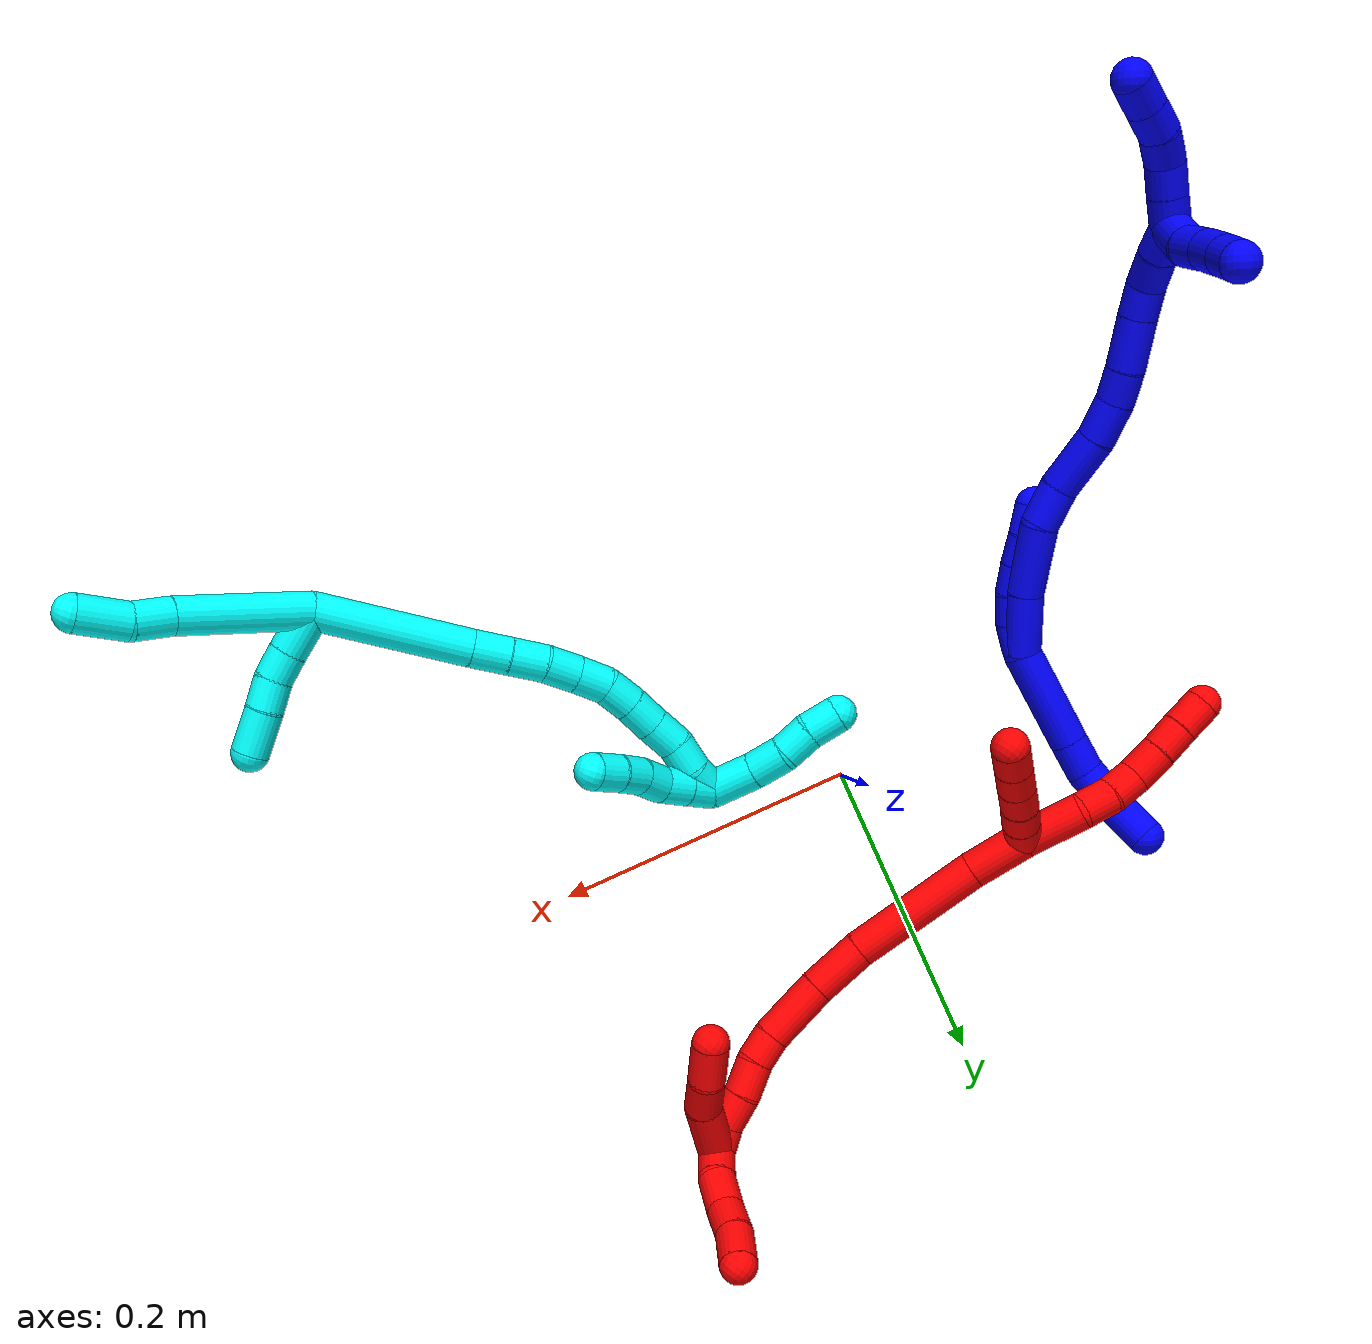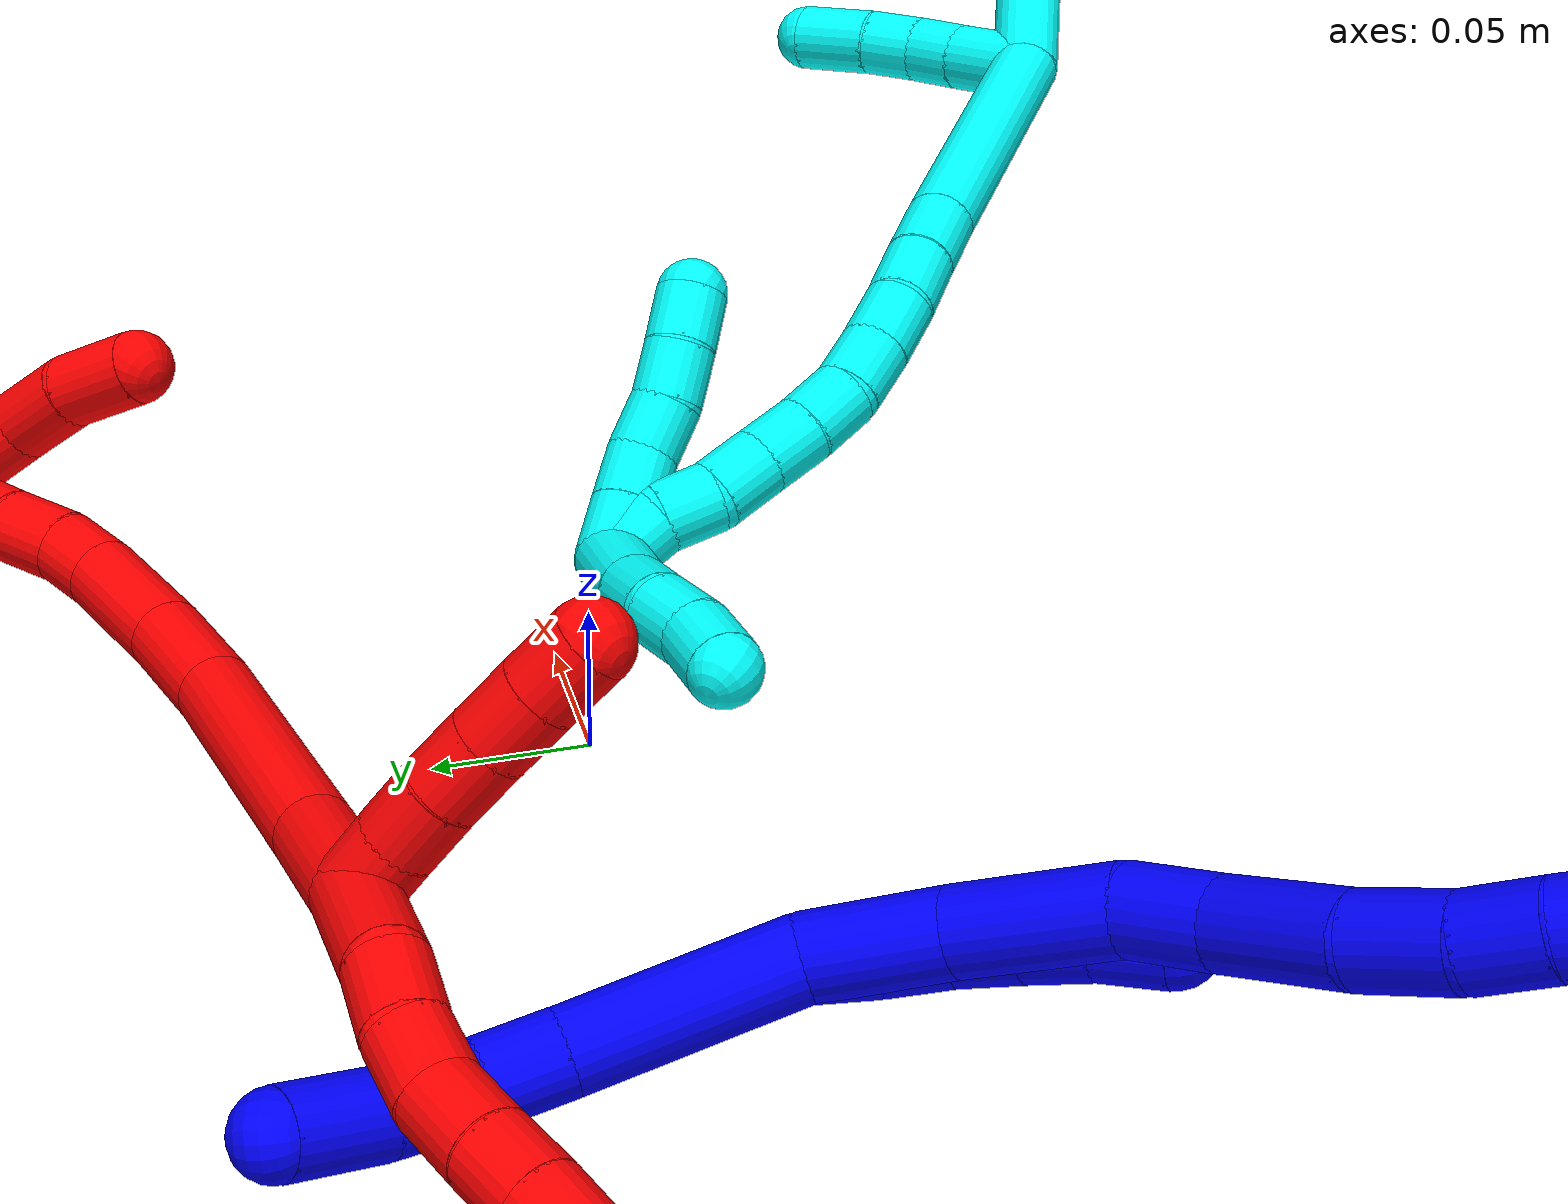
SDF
<sdf version="1.7">
 <world name="default">
  <plugin name="TubeGeneratorPlugin" filename="libtube_generator_plugin.so"/>
  <model name="photoneo_s_sensor">
   <static>1</static>
   <pose>0 0 2 1.57079 1.57079 3.14159</pose>
   <link name="link">
    <inertial><mass>0.1</mass></inertial>
    <sensor name="sensor" type="depth">
     <update_rate>30</update_rate>
     <camera>
      <horizontal_fov>1.22</horizontal_fov>
      <image><width>1920</width><height>1200</height><format>B8G8R8</format></image>
      <clip><near>0.1</near><far>4</far></clip>
      <depth_camera><output>points</output></depth_camera>
     </camera>
     <plugin name="camera_plugin" filename="libgazebo_ros_depth_camera.so">
      <baseline>0.2</baseline>
      <alwaysOn>1</alwaysOn>
      <updateRate>0.0</updateRate>
      <cameraName>camera_ir</cameraName>
      <imageTopicName>/camera/color/image_raw</imageTopicName>
      <cameraInfoTopicName>/camera/color/camera_info</cameraInfoTopicName>
      <depthImageTopicName>/camera/depth/image_raw</depthImageTopicName>
      <depthImageCameraInfoTopicName>/camera/depth/camera_info</depthImageCameraInfoTopicName>
      <pointCloudTopicName>/camera/depth/points</pointCloudTopicName>
      <frameName>fr_optical</frameName>
      <pointCloudCutoff>0.1</pointCloudCutoff>
      <pointCloudCutoffMax>2.0</pointCloudCutoffMax>
      <distortionK1>0</distortionK1>
      <distortionK2>0</distortionK2>
      <distortionK3>0</distortionK3>
      <distortionT1>0</distortionT1>
      <distortionT2>0</distortionT2>
      <CxPrime>0</CxPrime>
      <Cx>0</Cx>
      <Cy>0</Cy>
      <focalLength>0</focalLength>
      <hackBaseline>0</hackBaseline>
     </plugin>
    </sensor>
   </link>
  </model>
  <gravity>0 0 -9.8</gravity>
  <magnetic_field>6e-06 2.3e-05 -4.2e-05</magnetic_field>
  <atmosphere type="adiabatic"/>
  <physics name="default_physics" default="0" type="ode">
   <max_step_size>0.003</max_step_size>
   <real_time_factor>1</real_time_factor>
   <real_time_update_rate>1000</real_time_update_rate>
   <max_contacts>10000</max_contacts>
   <ode>
    <solver>
     <type>quick</type>
     <iters>100</iters>
     <sor>1.3</sor>
     <use_dynamic_moi_rescaling>0</use_dynamic_moi_rescaling>
    </solver>
    <constraints>
     <contact_max_correcting_vel>0</contact_max_correcting_vel>
     <contact_surface_layer>0.001</contact_surface_layer>
     <cfm>0</cfm>
     <erp>0.2</erp>
    </constraints>
   </ode>
  </physics>
  <scene><ambient>0.4 0.4 0.4 1</ambient><background>0.7 0.7 0.7 1</background><shadows>0</shadows></scene>
  <audio><device>default</device></audio>
  <spherical_coordinates>
   <surface_model>EARTH_WGS84</surface_model>
   <latitude_deg>0</latitude_deg>
   <longitude_deg>0</longitude_deg>
   <elevation>0</elevation>
   <heading_deg>0</heading_deg>
  </spherical_coordinates>
  <model name="bin">
   <static>1</static>
   <link name="bottom">
    <collision name="collision-bottom">
     <pose>0 0 -0.01 0 -0 0</pose>
     <geometry><box><size>0.8 0.6 0.02</size></box></geometry>
     <surface>
      <friction><ode><mu>100</mu><mu2>100</mu2></ode></friction>
      <contact><collide_bitmask>65535</collide_bitmask></contact>
     </surface>
    </collision>
   </link>
   <link name="west_wall">
    <collision name="collision-west_wall">
     <pose>-0.41 0 0.1 0 -0 0</pose>
     <geometry><box><size>0.02 0.6 0.2</size></box></geometry>
     <surface>
      <friction><ode><mu>100</mu><mu2>100</mu2></ode></friction>
      <contact><collide_bitmask>65535</collide_bitmask></contact>
     </surface>
    </collision>
   </link>
   <link name="east_wall">
    <collision name="collision-east_wall">
     <pose>0.41 0 0.1 0 -0 0</pose>
     <geometry><box><size>0.02 0.6 0.2</size></box></geometry>
     <surface>
      <friction><ode><mu>100</mu><mu2>100</mu2></ode></friction>
      <contact><collide_bitmask>65535</collide_bitmask></contact>
     </surface>
    </collision>
   </link>
   <link name="south_wall">
    <collision name="collision-south_wall">
     <pose>0 -0.31 0.1 0 -0 0</pose>
     <geometry><box><size>0.8 0.02 0.2</size></box></geometry>
     <surface>
      <friction><ode><mu>100</mu><mu2>100</mu2></ode></friction>
      <contact><collide_bitmask>65535</collide_bitmask></contact>
     </surface>
    </collision>
   </link>
   <link name="north_wall">
    <collision name="collision-north_wall">
     <pose>0 0.31 0.1 0 -0 0</pose>
     <geometry><box><size>0.8 0.02 0.2</size></box></geometry>
     <surface>
      <friction><ode><mu>100</mu><mu2>100</mu2></ode></friction>
      <contact><collide_bitmask>65535</collide_bitmask></contact>
     </surface>
    </collision>
   </link>
  </model>
  <model name="1">
   <static>0</static>
   <link name="1">
    <collision name="collision-cylinder-e_1_2_8">
     <pose>0.01453 -0.000638 -0.030643 3.12078 0.442671 3.04915</pose>
     <geometry><cylinder><radius>0.0125</radius><length>0.067839</length></cylinder></geometry>
     <surface>
      <friction><ode><mu>1.16</mu><mu2>1.16</mu2><slip1>0</slip1><slip2>0</slip2></ode></friction>
      <contact><ode><kp>1e+06</kp><kd>1</kd><max_vel>0</max_vel><min_depth>0.001</min_depth></ode></contact>
     </surface>
    </collision>
    <visual name="visual-cylinder-e_1_2_8">
     <pose>0.01453 -0.000638 -0.030643 3.12078 0.442671 3.04915</pose>
     <geometry><cylinder><radius>0.0125</radius><length>0.067839</length></cylinder></geometry>
     <material><ambient>0 0 1 1</ambient></material>
    </visual>
    <collision name="collision-cylinder-e_2_8_9">
     <pose>0.034278 -0.001905 -0.072082 3.08335 0.44965 2.8882</pose>
     <geometry><cylinder><radius>0.0125</radius><length>0.024014</length></cylinder></geometry>
     <surface>
      <friction><ode><mu>1.16</mu><mu2>1.16</mu2><slip1>0</slip1><slip2>0</slip2></ode></friction>
      <contact><ode><kp>1e+06</kp><kd>1</kd><max_vel>0</max_vel><min_depth>0.001</min_depth></ode></contact>
     </surface>
    </collision>
    <visual name="visual-cylinder-e_2_8_9">
     <pose>0.034278 -0.001905 -0.072082 3.08335 0.44965 2.8882</pose>
     <geometry><cylinder><radius>0.0125</radius><length>0.024014</length></cylinder></geometry>
     <material><ambient>0 0 1 1</ambient></material>
    </visual>
    <collision name="collision-cylinder-e_3_9_10">
     <pose>0.047265 -0.006548 -0.093408 2.77749 0.603508 2.07339</pose>
     <geometry><cylinder><radius>0.0125</radius><length>0.027376</length></cylinder></geometry>
     <surface>
      <friction><ode><mu>1.16</mu><mu2>1.16</mu2><slip1>0</slip1><slip2>0</slip2></ode></friction>
      <contact><ode><kp>1e+06</kp><kd>1</kd><max_vel>0</max_vel><min_depth>0.001</min_depth></ode></contact>
     </surface>
    </collision>
    <visual name="visual-cylinder-e_3_9_10">
     <pose>0.047265 -0.006548 -0.093408 2.77749 0.603508 2.07339</pose>
     <geometry><cylinder><radius>0.0125</radius><length>0.027376</length></cylinder></geometry>
     <material><ambient>0 0 1 1</ambient></material>
    </visual>
    <collision name="collision-cylinder-e_4_10_6">
     <pose>0.064042 -0.017705 -0.114163 2.53174 0.625537 1.59787</pose>
     <geometry><cylinder><radius>0.0125</radius><length>0.030771</length></cylinder></geometry>
     <surface>
      <friction><ode><mu>1.16</mu><mu2>1.16</mu2><slip1>0</slip1><slip2>0</slip2></ode></friction>
      <contact><ode><kp>1e+06</kp><kd>1</kd><max_vel>0</max_vel><min_depth>0.001</min_depth></ode></contact>
     </surface>
    </collision>
    <visual name="visual-cylinder-e_4_10_6">
     <pose>0.064042 -0.017705 -0.114163 2.53174 0.625537 1.59787</pose>
     <geometry><cylinder><radius>0.0125</radius><length>0.030771</length></cylinder></geometry>
     <material><ambient>0 0 1 1</ambient></material>
    </visual>
    <collision name="collision-cylinder-e_1_2_11">
     <pose>-0.001826 0.001794 0.009667 -0.183493 -0.183659 0.016945</pose>
     <geometry><cylinder><radius>0.0125</radius><length>0.02</length></cylinder></geometry>
     <surface>
      <friction><ode><mu>1.16</mu><mu2>1.16</mu2><slip1>0</slip1><slip2>0</slip2></ode></friction>
      <contact><ode><kp>1e+06</kp><kd>1</kd><max_vel>0</max_vel><min_depth>0.001</min_depth></ode></contact>
     </surface>
    </collision>
    <visual name="visual-cylinder-e_1_2_11">
     <pose>-0.001826 0.001794 0.009667 -0.183493 -0.183659 0.016945</pose>
     <geometry><cylinder><radius>0.0125</radius><length>0.02</length></cylinder></geometry>
     <material><ambient>0 0 1 1</ambient></material>
    </visual>
    <collision name="collision-cylinder-e_2_11_12">
     <pose>-0.003669 0.002736 0.029297 0.085317 -0.001689 -7.2e-05</pose>
     <geometry><cylinder><radius>0.0125</radius><length>0.02</length></cylinder></geometry>
     <surface>
      <friction><ode><mu>1.16</mu><mu2>1.16</mu2><slip1>0</slip1><slip2>0</slip2></ode></friction>
      <contact><ode><kp>1e+06</kp><kd>1</kd><max_vel>0</max_vel><min_depth>0.001</min_depth></ode></contact>
     </surface>
    </collision>
    <visual name="visual-cylinder-e_2_11_12">
     <pose>-0.003669 0.002736 0.029297 0.085317 -0.001689 -7.2e-05</pose>
     <geometry><cylinder><radius>0.0125</radius><length>0.02</length></cylinder></geometry>
     <material><ambient>0 0 1 1</ambient></material>
    </visual>
    <collision name="collision-cylinder-e_3_12_13">
     <pose>-0.001847 0.000377 0.048974 0.153846 0.184991 0.014299</pose>
     <geometry><cylinder><radius>0.0125</radius><length>0.02</length></cylinder></geometry>
     <surface>
      <friction><ode><mu>1.16</mu><mu2>1.16</mu2><slip1>0</slip1><slip2>0</slip2></ode></friction>
      <contact><ode><kp>1e+06</kp><kd>1</kd><max_vel>0</max_vel><min_depth>0.001</min_depth></ode></contact>
     </surface>
    </collision>
    <visual name="visual-cylinder-e_3_12_13">
     <pose>-0.001847 0.000377 0.048974 0.153846 0.184991 0.014299</pose>
     <geometry><cylinder><radius>0.0125</radius><length>0.02</length></cylinder></geometry>
     <material><ambient>0 0 1 1</ambient></material>
    </visual>
    <collision name="collision-cylinder-e_4_13_14">
     <pose>0.002414 -0.002925 0.068222 0.186234 0.244569 0.022953</pose>
     <geometry><cylinder><radius>0.0125</radius><length>0.02</length></cylinder></geometry>
     <surface>
      <friction><ode><mu>1.16</mu><mu2>1.16</mu2><slip1>0</slip1><slip2>0</slip2></ode></friction>
      <contact><ode><kp>1e+06</kp><kd>1</kd><max_vel>0</max_vel><min_depth>0.001</min_depth></ode></contact>
     </surface>
    </collision>
    <visual name="visual-cylinder-e_4_13_14">
     <pose>0.002414 -0.002925 0.068222 0.186234 0.244569 0.022953</pose>
     <geometry><cylinder><radius>0.0125</radius><length>0.02</length></cylinder></geometry>
     <material><ambient>0 0 1 1</ambient></material>
    </visual>
    <collision name="collision-cylinder-e_5_14_5">
     <pose>0.007364 -0.004656 0.087431 -0.006779 0.255676 -0.000871</pose>
     <geometry><cylinder><radius>0.0125</radius><length>0.02</length></cylinder></geometry>
     <surface>
      <friction><ode><mu>1.16</mu><mu2>1.16</mu2><slip1>0</slip1><slip2>0</slip2></ode></friction>
      <contact><ode><kp>1e+06</kp><kd>1</kd><max_vel>0</max_vel><min_depth>0.001</min_depth></ode></contact>
     </surface>
    </collision>
    <visual name="visual-cylinder-e_5_14_5">
     <pose>0.007364 -0.004656 0.087431 -0.006779 0.255676 -0.000871</pose>
     <geometry><cylinder><radius>0.0125</radius><length>0.02</length></cylinder></geometry>
     <material><ambient>0 0 1 1</ambient></material>
    </visual>
    <collision name="collision-cylinder-e_1_2_15">
     <pose>0.000797 -0.003277 0.020419 0.159124 0.038528 0.003072</pose>
     <geometry><cylinder><radius>0.0125</radius><length>0.041391</length></cylinder></geometry>
     <surface>
      <friction><ode><mu>1.16</mu><mu2>1.16</mu2><slip1>0</slip1><slip2>0</slip2></ode></friction>
      <contact><ode><kp>1e+06</kp><kd>1</kd><max_vel>0</max_vel><min_depth>0.001</min_depth></ode></contact>
     </surface>
    </collision>
    <visual name="visual-cylinder-e_1_2_15">
     <pose>0.000797 -0.003277 0.020419 0.159124 0.038528 0.003072</pose>
     <geometry><cylinder><radius>0.0125</radius><length>0.041391</length></cylinder></geometry>
     <material><ambient>0 0 1 1</ambient></material>
    </visual>
    <collision name="collision-cylinder-e_2_15_16">
     <pose>0.005779 -0.011992 0.063606 0.23448 0.176881 0.020887</pose>
     <geometry><cylinder><radius>0.0125</radius><length>0.04756</length></cylinder></geometry>
     <surface>
      <friction><ode><mu>1.16</mu><mu2>1.16</mu2><slip1>0</slip1><slip2>0</slip2></ode></friction>
      <contact><ode><kp>1e+06</kp><kd>1</kd><max_vel>0</max_vel><min_depth>0.001</min_depth></ode></contact>
     </surface>
    </collision>
    <visual name="visual-cylinder-e_2_15_16">
     <pose>0.005779 -0.011992 0.063606 0.23448 0.176881 0.020887</pose>
     <geometry><cylinder><radius>0.0125</radius><length>0.04756</length></cylinder></geometry>
     <material><ambient>0 0 1 1</ambient></material>
    </visual>
    <collision name="collision-cylinder-e_3_16_17">
     <pose>0.016089 -0.019441 0.09815 0.169007 0.47382 0.040897</pose>
     <geometry><cylinder><radius>0.0125</radius><length>0.02685</length></cylinder></geometry>
     <surface>
      <friction><ode><mu>1.16</mu><mu2>1.16</mu2><slip1>0</slip1><slip2>0</slip2></ode></friction>
      <contact><ode><kp>1e+06</kp><kd>1</kd><max_vel>0</max_vel><min_depth>0.001</min_depth></ode></contact>
     </surface>
    </collision>
    <visual name="visual-cylinder-e_3_16_17">
     <pose>0.016089 -0.019441 0.09815 0.169007 0.47382 0.040897</pose>
     <geometry><cylinder><radius>0.0125</radius><length>0.02685</length></cylinder></geometry>
     <material><ambient>0 0 1 1</ambient></material>
    </visual>
    <collision name="collision-cylinder-e_4_17_18">
     <pose>0.032946 -0.027366 0.125147 0.37069 0.5814 0.112071</pose>
     <geometry><cylinder><radius>0.0125</radius><length>0.039082</length></cylinder></geometry>
     <surface>
      <friction><ode><mu>1.16</mu><mu2>1.16</mu2><slip1>0</slip1><slip2>0</slip2></ode></friction>
      <contact><ode><kp>1e+06</kp><kd>1</kd><max_vel>0</max_vel><min_depth>0.001</min_depth></ode></contact>
     </surface>
    </collision>
    <visual name="visual-cylinder-e_4_17_18">
     <pose>0.032946 -0.027366 0.125147 0.37069 0.5814 0.112071</pose>
     <geometry><cylinder><radius>0.0125</radius><length>0.039082</length></cylinder></geometry>
     <material><ambient>0 0 1 1</ambient></material>
    </visual>
    <collision name="collision-cylinder-e_5_18_19">
     <pose>0.049066 -0.036817 0.152057 0.293737 0.415493 0.062345</pose>
     <geometry><cylinder><radius>0.0125</radius><length>0.026696</length></cylinder></geometry>
     <surface>
      <friction><ode><mu>1.16</mu><mu2>1.16</mu2><slip1>0</slip1><slip2>0</slip2></ode></friction>
      <contact><ode><kp>1e+06</kp><kd>1</kd><max_vel>0</max_vel><min_depth>0.001</min_depth></ode></contact>
     </surface>
    </collision>
    <visual name="visual-cylinder-e_5_18_19">
     <pose>0.049066 -0.036817 0.152057 0.293737 0.415493 0.062345</pose>
     <geometry><cylinder><radius>0.0125</radius><length>0.026696</length></cylinder></geometry>
     <material><ambient>0 0 1 1</ambient></material>
    </visual>
    <collision name="collision-cylinder-e_6_19_20">
     <pose>0.056954 -0.043775 0.173785 0.328516 0.231592 0.038554</pose>
     <geometry><cylinder><radius>0.0125</radius><length>0.021793</length></cylinder></geometry>
     <surface>
      <friction><ode><mu>1.16</mu><mu2>1.16</mu2><slip1>0</slip1><slip2>0</slip2></ode></friction>
      <contact><ode><kp>1e+06</kp><kd>1</kd><max_vel>0</max_vel><min_depth>0.001</min_depth></ode></contact>
     </surface>
    </collision>
    <visual name="visual-cylinder-e_6_19_20">
     <pose>0.056954 -0.043775 0.173785 0.328516 0.231592 0.038554</pose>
     <geometry><cylinder><radius>0.0125</radius><length>0.021793</length></cylinder></geometry>
     <material><ambient>0 0 1 1</ambient></material>
    </visual>
    <collision name="collision-cylinder-e_7_20_21">
     <pose>0.062503 -0.051219 0.199838 0.246059 0.182511 0.02263</pose>
     <geometry><cylinder><radius>0.0125</radius><length>0.033582</length></cylinder></geometry>
     <surface>
      <friction><ode><mu>1.16</mu><mu2>1.16</mu2><slip1>0</slip1><slip2>0</slip2></ode></friction>
      <contact><ode><kp>1e+06</kp><kd>1</kd><max_vel>0</max_vel><min_depth>0.001</min_depth></ode></contact>
     </surface>
    </collision>
    <visual name="visual-cylinder-e_7_20_21">
     <pose>0.062503 -0.051219 0.199838 0.246059 0.182511 0.02263</pose>
     <geometry><cylinder><radius>0.0125</radius><length>0.033582</length></cylinder></geometry>
     <material><ambient>0 0 1 1</ambient></material>
    </visual>
    <collision name="collision-cylinder-e_8_21_22">
     <pose>0.067465 -0.058487 0.225447 0.326293 0.186794 0.030835</pose>
     <geometry><cylinder><radius>0.0125</radius><length>0.020615</length></cylinder></geometry>
     <surface>
      <friction><ode><mu>1.16</mu><mu2>1.16</mu2><slip1>0</slip1><slip2>0</slip2></ode></friction>
      <contact><ode><kp>1e+06</kp><kd>1</kd><max_vel>0</max_vel><min_depth>0.001</min_depth></ode></contact>
     </surface>
    </collision>
    <visual name="visual-cylinder-e_8_21_22">
     <pose>0.067465 -0.058487 0.225447 0.326293 0.186794 0.030835</pose>
     <geometry><cylinder><radius>0.0125</radius><length>0.020615</length></cylinder></geometry>
     <material><ambient>0 0 1 1</ambient></material>
    </visual>
    <collision name="collision-cylinder-e_9_22_23">
     <pose>0.070984 -0.068434 0.243724 0.657174 0.145272 0.049607</pose>
     <geometry><cylinder><radius>0.0125</radius><length>0.02217</length></cylinder></geometry>
     <surface>
      <friction><ode><mu>1.16</mu><mu2>1.16</mu2><slip1>0</slip1><slip2>0</slip2></ode></friction>
      <contact><ode><kp>1e+06</kp><kd>1</kd><max_vel>0</max_vel><min_depth>0.001</min_depth></ode></contact>
     </surface>
    </collision>
    <visual name="visual-cylinder-e_9_22_23">
     <pose>0.070984 -0.068434 0.243724 0.657174 0.145272 0.049607</pose>
     <geometry><cylinder><radius>0.0125</radius><length>0.02217</length></cylinder></geometry>
     <material><ambient>0 0 1 1</ambient></material>
    </visual>
    <collision name="collision-cylinder-e_10_23_1">
     <pose>0.074889 -0.081071 0.260288 0.645632 0.229075 0.076928</pose>
     <geometry><cylinder><radius>0.0125</radius><length>0.020261</length></cylinder></geometry>
     <surface>
      <friction><ode><mu>1.16</mu><mu2>1.16</mu2><slip1>0</slip1><slip2>0</slip2></ode></friction>
      <contact><ode><kp>1e+06</kp><kd>1</kd><max_vel>0</max_vel><min_depth>0.001</min_depth></ode></contact>
     </surface>
    </collision>
    <visual name="visual-cylinder-e_10_23_1">
     <pose>0.074889 -0.081071 0.260288 0.645632 0.229075 0.076928</pose>
     <geometry><cylinder><radius>0.0125</radius><length>0.020261</length></cylinder></geometry>
     <material><ambient>0 0 1 1</ambient></material>
    </visual>
    <collision name="collision-cylinder-e_1_1_24">
     <pose>0.077631 -0.100973 0.262518 1.95525 0.029293 0.043448</pose>
     <geometry><cylinder><radius>0.0125</radius><length>0.030143</length></cylinder></geometry>
     <surface>
      <friction><ode><mu>1.16</mu><mu2>1.16</mu2><slip1>0</slip1><slip2>0</slip2></ode></friction>
      <contact><ode><kp>1e+06</kp><kd>1</kd><max_vel>0</max_vel><min_depth>0.001</min_depth></ode></contact>
     </surface>
    </collision>
    <visual name="visual-cylinder-e_1_1_24">
     <pose>0.077631 -0.100973 0.262518 1.95525 0.029293 0.043448</pose>
     <geometry><cylinder><radius>0.0125</radius><length>0.030143</length></cylinder></geometry>
     <material><ambient>0 0 1 1</ambient></material>
    </visual>
    <collision name="collision-cylinder-e_2_24_25">
     <pose>0.080686 -0.125766 0.255517 1.6949 0.235135 0.265943</pose>
     <geometry><cylinder><radius>0.0125</radius><length>0.022441</length></cylinder></geometry>
     <surface>
      <friction><ode><mu>1.16</mu><mu2>1.16</mu2><slip1>0</slip1><slip2>0</slip2></ode></friction>
      <contact><ode><kp>1e+06</kp><kd>1</kd><max_vel>0</max_vel><min_depth>0.001</min_depth></ode></contact>
     </surface>
    </collision>
    <visual name="visual-cylinder-e_2_24_25">
     <pose>0.080686 -0.125766 0.255517 1.6949 0.235135 0.265943</pose>
     <geometry><cylinder><radius>0.0125</radius><length>0.022441</length></cylinder></geometry>
     <material><ambient>0 0 1 1</ambient></material>
    </visual>
    <collision name="collision-cylinder-e_3_25_26">
     <pose>0.084461 -0.149363 0.252408 1.70768 0.089838 0.103038</pose>
     <geometry><cylinder><radius>0.0125</radius><length>0.025882</length></cylinder></geometry>
     <surface>
      <friction><ode><mu>1.16</mu><mu2>1.16</mu2><slip1>0</slip1><slip2>0</slip2></ode></friction>
      <contact><ode><kp>1e+06</kp><kd>1</kd><max_vel>0</max_vel><min_depth>0.001</min_depth></ode></contact>
     </surface>
    </collision>
    <visual name="visual-cylinder-e_3_25_26">
     <pose>0.084461 -0.149363 0.252408 1.70768 0.089838 0.103038</pose>
     <geometry><cylinder><radius>0.0125</radius><length>0.025882</length></cylinder></geometry>
     <material><ambient>0 0 1 1</ambient></material>
    </visual>
    <collision name="collision-cylinder-e_4_26_4">
     <pose>0.086181 -0.172755 0.248998 1.72494 0.051936 0.060624</pose>
     <geometry><cylinder><radius>0.0125</radius><length>0.021533</length></cylinder></geometry>
     <surface>
      <friction><ode><mu>1.16</mu><mu2>1.16</mu2><slip1>0</slip1><slip2>0</slip2></ode></friction>
      <contact><ode><kp>1e+06</kp><kd>1</kd><max_vel>0</max_vel><min_depth>0.001</min_depth></ode></contact>
     </surface>
    </collision>
    <visual name="visual-cylinder-e_4_26_4">
     <pose>0.086181 -0.172755 0.248998 1.72494 0.051936 0.060624</pose>
     <geometry><cylinder><radius>0.0125</radius><length>0.021533</length></cylinder></geometry>
     <material><ambient>0 0 1 1</ambient></material>
    </visual>
    <collision name="collision-cylinder-e_1_1_27">
     <pose>0.075581 -0.089696 0.277665 0.275966 -0.161512 -0.022476</pose>
     <geometry><cylinder><radius>0.0125</radius><length>0.02</length></cylinder></geometry>
     <surface>
      <friction><ode><mu>1.16</mu><mu2>1.16</mu2><slip1>0</slip1><slip2>0</slip2></ode></friction>
      <contact><ode><kp>1e+06</kp><kd>1</kd><max_vel>0</max_vel><min_depth>0.001</min_depth></ode></contact>
     </surface>
    </collision>
    <visual name="visual-cylinder-e_1_1_27">
     <pose>0.075581 -0.089696 0.277665 0.275966 -0.161512 -0.022476</pose>
     <geometry><cylinder><radius>0.0125</radius><length>0.02</length></cylinder></geometry>
     <material><ambient>0 0 1 1</ambient></material>
    </visual>
    <collision name="collision-cylinder-e_2_27_28">
     <pose>0.07255 -0.095137 0.29667 0.281624 -0.142793 -0.020275</pose>
     <geometry><cylinder><radius>0.0125</radius><length>0.02</length></cylinder></geometry>
     <surface>
      <friction><ode><mu>1.16</mu><mu2>1.16</mu2><slip1>0</slip1><slip2>0</slip2></ode></friction>
      <contact><ode><kp>1e+06</kp><kd>1</kd><max_vel>0</max_vel><min_depth>0.001</min_depth></ode></contact>
     </surface>
    </collision>
    <visual name="visual-cylinder-e_2_27_28">
     <pose>0.07255 -0.095137 0.29667 0.281624 -0.142793 -0.020275</pose>
     <geometry><cylinder><radius>0.0125</radius><length>0.02</length></cylinder></geometry>
     <material><ambient>0 0 1 1</ambient></material>
    </visual>
    <collision name="collision-cylinder-e_3_28_29">
     <pose>0.06805 -0.102927 0.314249 0.55815 -0.312776 -0.090303</pose>
     <geometry><cylinder><radius>0.0125</radius><length>0.02</length></cylinder></geometry>
     <surface>
      <friction><ode><mu>1.16</mu><mu2>1.16</mu2><slip1>0</slip1><slip2>0</slip2></ode></friction>
      <contact><ode><kp>1e+06</kp><kd>1</kd><max_vel>0</max_vel><min_depth>0.001</min_depth></ode></contact>
     </surface>
    </collision>
    <visual name="visual-cylinder-e_3_28_29">
     <pose>0.06805 -0.102927 0.314249 0.55815 -0.312776 -0.090303</pose>
     <geometry><cylinder><radius>0.0125</radius><length>0.02</length></cylinder></geometry>
     <material><ambient>0 0 1 1</ambient></material>
    </visual>
    <collision name="collision-cylinder-e_4_29_30">
     <pose>0.059854 -0.112272 0.329754 0.524976 -0.537319 -0.147679</pose>
     <geometry><cylinder><radius>0.0125</radius><length>0.02</length></cylinder></geometry>
     <surface>
      <friction><ode><mu>1.16</mu><mu2>1.16</mu2><slip1>0</slip1><slip2>0</slip2></ode></friction>
      <contact><ode><kp>1e+06</kp><kd>1</kd><max_vel>0</max_vel><min_depth>0.001</min_depth></ode></contact>
     </surface>
    </collision>
    <visual name="visual-cylinder-e_4_29_30">
     <pose>0.059854 -0.112272 0.329754 0.524976 -0.537319 -0.147679</pose>
     <geometry><cylinder><radius>0.0125</radius><length>0.02</length></cylinder></geometry>
     <material><ambient>0 0 1 1</ambient></material>
    </visual>
    <collision name="collision-cylinder-e_5_30_3">
     <pose>0.0496 -0.120868 0.344618 0.523619 -0.539331 -0.147857</pose>
     <geometry><cylinder><radius>0.0125</radius><length>0.02</length></cylinder></geometry>
     <surface>
      <friction><ode><mu>1.16</mu><mu2>1.16</mu2><slip1>0</slip1><slip2>0</slip2></ode></friction>
      <contact><ode><kp>1e+06</kp><kd>1</kd><max_vel>0</max_vel><min_depth>0.001</min_depth></ode></contact>
     </surface>
    </collision>
    <visual name="visual-cylinder-e_5_30_3">
     <pose>0.0496 -0.120868 0.344618 0.523619 -0.539331 -0.147857</pose>
     <geometry><cylinder><radius>0.0125</radius><length>0.02</length></cylinder></geometry>
     <material><ambient>0 0 1 1</ambient></material>
    </visual>
    <collision name="collision-sphere-3">
     <pose>0.044465 -0.125158 0.352049 0 -0 0</pose>
     <geometry><sphere><radius>0.0125</radius></sphere></geometry>
     <surface>
      <friction><ode><mu>1.16</mu><mu2>1.16</mu2><slip1>0</slip1><slip2>0</slip2></ode></friction>
      <contact><ode><kp>1e+06</kp><kd>1</kd><max_vel>0</max_vel><min_depth>0.001</min_depth></ode></contact>
     </surface>
    </collision>
    <visual name="visual-sphere-3">
     <pose>0.044465 -0.125158 0.352049 0 -0 0</pose>
     <geometry><sphere><radius>0.0125</radius></sphere></geometry>
     <material><ambient>0 0 1 1</ambient></material>
    </visual>
    <collision name="collision-sphere-30">
     <pose>0.054736 -0.116577 0.337187 0 -0 0</pose>
     <geometry><sphere><radius>0.0125</radius></sphere></geometry>
     <surface>
      <friction><ode><mu>1.16</mu><mu2>1.16</mu2><slip1>0</slip1><slip2>0</slip2></ode></friction>
      <contact><ode><kp>1e+06</kp><kd>1</kd><max_vel>0</max_vel><min_depth>0.001</min_depth></ode></contact>
     </surface>
    </collision>
    <visual name="visual-sphere-30">
     <pose>0.054736 -0.116577 0.337187 0 -0 0</pose>
     <geometry><sphere><radius>0.0125</radius></sphere></geometry>
     <material><ambient>0 0 1 1</ambient></material>
    </visual>
    <collision name="collision-sphere-29">
     <pose>0.064973 -0.107966 0.32232 0 -0 0</pose>
     <geometry><sphere><radius>0.0125</radius></sphere></geometry>
     <surface>
      <friction><ode><mu>1.16</mu><mu2>1.16</mu2><slip1>0</slip1><slip2>0</slip2></ode></friction>
      <contact><ode><kp>1e+06</kp><kd>1</kd><max_vel>0</max_vel><min_depth>0.001</min_depth></ode></contact>
     </surface>
    </collision>
    <visual name="visual-sphere-29">
     <pose>0.064973 -0.107966 0.32232 0 -0 0</pose>
     <geometry><sphere><radius>0.0125</radius></sphere></geometry>
     <material><ambient>0 0 1 1</ambient></material>
    </visual>
    <collision name="collision-sphere-28">
     <pose>0.071127 -0.097888 0.306178 0 -0 0</pose>
     <geometry><sphere><radius>0.0125</radius></sphere></geometry>
     <surface>
      <friction><ode><mu>1.16</mu><mu2>1.16</mu2><slip1>0</slip1><slip2>0</slip2></ode></friction>
      <contact><ode><kp>1e+06</kp><kd>1</kd><max_vel>0</max_vel><min_depth>0.001</min_depth></ode></contact>
     </surface>
    </collision>
    <visual name="visual-sphere-28">
     <pose>0.071127 -0.097888 0.306178 0 -0 0</pose>
     <geometry><sphere><radius>0.0125</radius></sphere></geometry>
     <material><ambient>0 0 1 1</ambient></material>
    </visual>
    <collision name="collision-sphere-27">
     <pose>0.073973 -0.092386 0.287161 0 -0 0</pose>
     <geometry><sphere><radius>0.0125</radius></sphere></geometry>
     <surface>
      <friction><ode><mu>1.16</mu><mu2>1.16</mu2><slip1>0</slip1><slip2>0</slip2></ode></friction>
      <contact><ode><kp>1e+06</kp><kd>1</kd><max_vel>0</max_vel><min_depth>0.001</min_depth></ode></contact>
     </surface>
    </collision>
    <visual name="visual-sphere-27">
     <pose>0.073973 -0.092386 0.287161 0 -0 0</pose>
     <geometry><sphere><radius>0.0125</radius></sphere></geometry>
     <material><ambient>0 0 1 1</ambient></material>
    </visual>
    <collision name="collision-sphere-4">
     <pose>0.08674 -0.18338 0.247347 0 -0 0</pose>
     <geometry><sphere><radius>0.0125</radius></sphere></geometry>
     <surface>
      <friction><ode><mu>1.16</mu><mu2>1.16</mu2><slip1>0</slip1><slip2>0</slip2></ode></friction>
      <contact><ode><kp>1e+06</kp><kd>1</kd><max_vel>0</max_vel><min_depth>0.001</min_depth></ode></contact>
     </surface>
    </collision>
    <visual name="visual-sphere-4">
     <pose>0.08674 -0.18338 0.247347 0 -0 0</pose>
     <geometry><sphere><radius>0.0125</radius></sphere></geometry>
     <material><ambient>0 0 1 1</ambient></material>
    </visual>
    <collision name="collision-sphere-26">
     <pose>0.085622 -0.162131 0.250649 0 -0 0</pose>
     <geometry><sphere><radius>0.0125</radius></sphere></geometry>
     <surface>
      <friction><ode><mu>1.16</mu><mu2>1.16</mu2><slip1>0</slip1><slip2>0</slip2></ode></friction>
      <contact><ode><kp>1e+06</kp><kd>1</kd><max_vel>0</max_vel><min_depth>0.001</min_depth></ode></contact>
     </surface>
    </collision>
    <visual name="visual-sphere-26">
     <pose>0.085622 -0.162131 0.250649 0 -0 0</pose>
     <geometry><sphere><radius>0.0125</radius></sphere></geometry>
     <material><ambient>0 0 1 1</ambient></material>
    </visual>
    <collision name="collision-sphere-25">
     <pose>0.0833 -0.136594 0.254166 0 -0 0</pose>
     <geometry><sphere><radius>0.0125</radius></sphere></geometry>
     <surface>
      <friction><ode><mu>1.16</mu><mu2>1.16</mu2><slip1>0</slip1><slip2>0</slip2></ode></friction>
      <contact><ode><kp>1e+06</kp><kd>1</kd><max_vel>0</max_vel><min_depth>0.001</min_depth></ode></contact>
     </surface>
    </collision>
    <visual name="visual-sphere-25">
     <pose>0.0833 -0.136594 0.254166 0 -0 0</pose>
     <geometry><sphere><radius>0.0125</radius></sphere></geometry>
     <material><ambient>0 0 1 1</ambient></material>
    </visual>
    <collision name="collision-sphere-24">
     <pose>0.078072 -0.114938 0.256868 0 -0 0</pose>
     <geometry><sphere><radius>0.0125</radius></sphere></geometry>
     <surface>
      <friction><ode><mu>1.16</mu><mu2>1.16</mu2><slip1>0</slip1><slip2>0</slip2></ode></friction>
      <contact><ode><kp>1e+06</kp><kd>1</kd><max_vel>0</max_vel><min_depth>0.001</min_depth></ode></contact>
     </surface>
    </collision>
    <visual name="visual-sphere-24">
     <pose>0.078072 -0.114938 0.256868 0 -0 0</pose>
     <geometry><sphere><radius>0.0125</radius></sphere></geometry>
     <material><ambient>0 0 1 1</ambient></material>
    </visual>
    <collision name="collision-sphere-1">
     <pose>0.077189 -0.087007 0.268169 0 -0 0</pose>
     <geometry><sphere><radius>0.0125</radius></sphere></geometry>
     <surface>
      <friction><ode><mu>1.16</mu><mu2>1.16</mu2><slip1>0</slip1><slip2>0</slip2></ode></friction>
      <contact><ode><kp>1e+06</kp><kd>1</kd><max_vel>0</max_vel><min_depth>0.001</min_depth></ode></contact>
     </surface>
    </collision>
    <visual name="visual-sphere-1">
     <pose>0.077189 -0.087007 0.268169 0 -0 0</pose>
     <geometry><sphere><radius>0.0125</radius></sphere></geometry>
     <material><ambient>0 0 1 1</ambient></material>
    </visual>
    <collision name="collision-sphere-23">
     <pose>0.072588 -0.075135 0.252408 0 -0 0</pose>
     <geometry><sphere><radius>0.0125</radius></sphere></geometry>
     <surface>
      <friction><ode><mu>1.16</mu><mu2>1.16</mu2><slip1>0</slip1><slip2>0</slip2></ode></friction>
      <contact><ode><kp>1e+06</kp><kd>1</kd><max_vel>0</max_vel><min_depth>0.001</min_depth></ode></contact>
     </surface>
    </collision>
    <visual name="visual-sphere-23">
     <pose>0.072588 -0.075135 0.252408 0 -0 0</pose>
     <geometry><sphere><radius>0.0125</radius></sphere></geometry>
     <material><ambient>0 0 1 1</ambient></material>
    </visual>
    <collision name="collision-sphere-22">
     <pose>0.069379 -0.061734 0.235041 0 -0 0</pose>
     <geometry><sphere><radius>0.0125</radius></sphere></geometry>
     <surface>
      <friction><ode><mu>1.16</mu><mu2>1.16</mu2><slip1>0</slip1><slip2>0</slip2></ode></friction>
      <contact><ode><kp>1e+06</kp><kd>1</kd><max_vel>0</max_vel><min_depth>0.001</min_depth></ode></contact>
     </surface>
    </collision>
    <visual name="visual-sphere-22">
     <pose>0.069379 -0.061734 0.235041 0 -0 0</pose>
     <geometry><sphere><radius>0.0125</radius></sphere></geometry>
     <material><ambient>0 0 1 1</ambient></material>
    </visual>
    <collision name="collision-sphere-21">
     <pose>0.065551 -0.055241 0.215853 0 -0 0</pose>
     <geometry><sphere><radius>0.0125</radius></sphere></geometry>
     <surface>
      <friction><ode><mu>1.16</mu><mu2>1.16</mu2><slip1>0</slip1><slip2>0</slip2></ode></friction>
      <contact><ode><kp>1e+06</kp><kd>1</kd><max_vel>0</max_vel><min_depth>0.001</min_depth></ode></contact>
     </surface>
    </collision>
    <visual name="visual-sphere-21">
     <pose>0.065551 -0.055241 0.215853 0 -0 0</pose>
     <geometry><sphere><radius>0.0125</radius></sphere></geometry>
     <material><ambient>0 0 1 1</ambient></material>
    </visual>
    <collision name="collision-sphere-11">
     <pose>-0.003653 0.003588 0.019334 0 -0 0</pose>
     <geometry><sphere><radius>0.0125</radius></sphere></geometry>
     <surface>
      <friction><ode><mu>1.16</mu><mu2>1.16</mu2><slip1>0</slip1><slip2>0</slip2></ode></friction>
      <contact><ode><kp>1e+06</kp><kd>1</kd><max_vel>0</max_vel><min_depth>0.001</min_depth></ode></contact>
     </surface>
    </collision>
    <visual name="visual-sphere-11">
     <pose>-0.003653 0.003588 0.019334 0 -0 0</pose>
     <geometry><sphere><radius>0.0125</radius></sphere></geometry>
     <material><ambient>0 0 1 1</ambient></material>
    </visual>
    <collision name="collision-sphere-6">
     <pose>0.073051 -0.024849 -0.124387 0 -0 0</pose>
     <geometry><sphere><radius>0.0125</radius></sphere></geometry>
     <surface>
      <friction><ode><mu>1.16</mu><mu2>1.16</mu2><slip1>0</slip1><slip2>0</slip2></ode></friction>
      <contact><ode><kp>1e+06</kp><kd>1</kd><max_vel>0</max_vel><min_depth>0.001</min_depth></ode></contact>
     </surface>
    </collision>
    <visual name="visual-sphere-6">
     <pose>0.073051 -0.024849 -0.124387 0 -0 0</pose>
     <geometry><sphere><radius>0.0125</radius></sphere></geometry>
     <material><ambient>0 0 1 1</ambient></material>
    </visual>
    <collision name="collision-sphere-10">
     <pose>0.055033 -0.010562 -0.103939 0 -0 0</pose>
     <geometry><sphere><radius>0.0125</radius></sphere></geometry>
     <surface>
      <friction><ode><mu>1.16</mu><mu2>1.16</mu2><slip1>0</slip1><slip2>0</slip2></ode></friction>
      <contact><ode><kp>1e+06</kp><kd>1</kd><max_vel>0</max_vel><min_depth>0.001</min_depth></ode></contact>
     </surface>
    </collision>
    <visual name="visual-sphere-10">
     <pose>0.055033 -0.010562 -0.103939 0 -0 0</pose>
     <geometry><sphere><radius>0.0125</radius></sphere></geometry>
     <material><ambient>0 0 1 1</ambient></material>
    </visual>
    <collision name="collision-sphere-9">
     <pose>0.039497 -0.002535 -0.082877 0 -0 0</pose>
     <geometry><sphere><radius>0.0125</radius></sphere></geometry>
     <surface>
      <friction><ode><mu>1.16</mu><mu2>1.16</mu2><slip1>0</slip1><slip2>0</slip2></ode></friction>
      <contact><ode><kp>1e+06</kp><kd>1</kd><max_vel>0</max_vel><min_depth>0.001</min_depth></ode></contact>
     </surface>
    </collision>
    <visual name="visual-sphere-9">
     <pose>0.039497 -0.002535 -0.082877 0 -0 0</pose>
     <geometry><sphere><radius>0.0125</radius></sphere></geometry>
     <material><ambient>0 0 1 1</ambient></material>
    </visual>
    <collision name="collision-sphere-2">
     <geometry><sphere><radius>0.0125</radius></sphere></geometry>
     <surface>
      <friction><ode><mu>1.16</mu><mu2>1.16</mu2><slip1>0</slip1><slip2>0</slip2></ode></friction>
      <contact><ode><kp>1e+06</kp><kd>1</kd><max_vel>0</max_vel><min_depth>0.001</min_depth></ode></contact>
     </surface>
    </collision>
    <visual name="visual-sphere-2">
     <geometry><sphere><radius>0.0125</radius></sphere></geometry>
     <material><ambient>0 0 1 1</ambient></material>
    </visual>
    <collision name="collision-sphere-19">
     <pose>0.054453 -0.040353 0.163747 0 -0 0</pose>
     <geometry><sphere><radius>0.0125</radius></sphere></geometry>
     <surface>
      <friction><ode><mu>1.16</mu><mu2>1.16</mu2><slip1>0</slip1><slip2>0</slip2></ode></friction>
      <contact><ode><kp>1e+06</kp><kd>1</kd><max_vel>0</max_vel><min_depth>0.001</min_depth></ode></contact>
     </surface>
    </collision>
    <visual name="visual-sphere-19">
     <pose>0.054453 -0.040353 0.163747 0 -0 0</pose>
     <geometry><sphere><radius>0.0125</radius></sphere></geometry>
     <material><ambient>0 0 1 1</ambient></material>
    </visual>
    <collision name="collision-sphere-8">
     <pose>0.029059 -0.001276 -0.061287 0 -0 0</pose>
     <geometry><sphere><radius>0.0125</radius></sphere></geometry>
     <surface>
      <friction><ode><mu>1.16</mu><mu2>1.16</mu2><slip1>0</slip1><slip2>0</slip2></ode></friction>
      <contact><ode><kp>1e+06</kp><kd>1</kd><max_vel>0</max_vel><min_depth>0.001</min_depth></ode></contact>
     </surface>
    </collision>
    <visual name="visual-sphere-8">
     <pose>0.029059 -0.001276 -0.061287 0 -0 0</pose>
     <geometry><sphere><radius>0.0125</radius></sphere></geometry>
     <material><ambient>0 0 1 1</ambient></material>
    </visual>
    <collision name="collision-sphere-12">
     <pose>-0.003686 0.001884 0.039261 0 -0 0</pose>
     <geometry><sphere><radius>0.0125</radius></sphere></geometry>
     <surface>
      <friction><ode><mu>1.16</mu><mu2>1.16</mu2><slip1>0</slip1><slip2>0</slip2></ode></friction>
      <contact><ode><kp>1e+06</kp><kd>1</kd><max_vel>0</max_vel><min_depth>0.001</min_depth></ode></contact>
     </surface>
    </collision>
    <visual name="visual-sphere-12">
     <pose>-0.003686 0.001884 0.039261 0 -0 0</pose>
     <geometry><sphere><radius>0.0125</radius></sphere></geometry>
     <material><ambient>0 0 1 1</ambient></material>
    </visual>
    <collision name="collision-sphere-13">
     <pose>-8e-06 -0.001129 0.058687 0 -0 0</pose>
     <geometry><sphere><radius>0.0125</radius></sphere></geometry>
     <surface>
      <friction><ode><mu>1.16</mu><mu2>1.16</mu2><slip1>0</slip1><slip2>0</slip2></ode></friction>
      <contact><ode><kp>1e+06</kp><kd>1</kd><max_vel>0</max_vel><min_depth>0.001</min_depth></ode></contact>
     </surface>
    </collision>
    <visual name="visual-sphere-13">
     <pose>-8e-06 -0.001129 0.058687 0 -0 0</pose>
     <geometry><sphere><radius>0.0125</radius></sphere></geometry>
     <material><ambient>0 0 1 1</ambient></material>
    </visual>
    <collision name="collision-sphere-14">
     <pose>0.004835 -0.004722 0.077757 0 -0 0</pose>
     <geometry><sphere><radius>0.0125</radius></sphere></geometry>
     <surface>
      <friction><ode><mu>1.16</mu><mu2>1.16</mu2><slip1>0</slip1><slip2>0</slip2></ode></friction>
      <contact><ode><kp>1e+06</kp><kd>1</kd><max_vel>0</max_vel><min_depth>0.001</min_depth></ode></contact>
     </surface>
    </collision>
    <visual name="visual-sphere-14">
     <pose>0.004835 -0.004722 0.077757 0 -0 0</pose>
     <geometry><sphere><radius>0.0125</radius></sphere></geometry>
     <material><ambient>0 0 1 1</ambient></material>
    </visual>
    <collision name="collision-sphere-5">
     <pose>0.009893 -0.004591 0.097106 0 -0 0</pose>
     <geometry><sphere><radius>0.0125</radius></sphere></geometry>
     <surface>
      <friction><ode><mu>1.16</mu><mu2>1.16</mu2><slip1>0</slip1><slip2>0</slip2></ode></friction>
      <contact><ode><kp>1e+06</kp><kd>1</kd><max_vel>0</max_vel><min_depth>0.001</min_depth></ode></contact>
     </surface>
    </collision>
    <visual name="visual-sphere-5">
     <pose>0.009893 -0.004591 0.097106 0 -0 0</pose>
     <geometry><sphere><radius>0.0125</radius></sphere></geometry>
     <material><ambient>0 0 1 1</ambient></material>
    </visual>
    <collision name="collision-sphere-15">
     <pose>0.001594 -0.006554 0.040838 0 -0 0</pose>
     <geometry><sphere><radius>0.0125</radius></sphere></geometry>
     <surface>
      <friction><ode><mu>1.16</mu><mu2>1.16</mu2><slip1>0</slip1><slip2>0</slip2></ode></friction>
      <contact><ode><kp>1e+06</kp><kd>1</kd><max_vel>0</max_vel><min_depth>0.001</min_depth></ode></contact>
     </surface>
    </collision>
    <visual name="visual-sphere-15">
     <pose>0.001594 -0.006554 0.040838 0 -0 0</pose>
     <geometry><sphere><radius>0.0125</radius></sphere></geometry>
     <material><ambient>0 0 1 1</ambient></material>
    </visual>
    <collision name="collision-sphere-16">
     <pose>0.009963 -0.017431 0.086375 0 -0 0</pose>
     <geometry><sphere><radius>0.0125</radius></sphere></geometry>
     <surface>
      <friction><ode><mu>1.16</mu><mu2>1.16</mu2><slip1>0</slip1><slip2>0</slip2></ode></friction>
      <contact><ode><kp>1e+06</kp><kd>1</kd><max_vel>0</max_vel><min_depth>0.001</min_depth></ode></contact>
     </surface>
    </collision>
    <visual name="visual-sphere-16">
     <pose>0.009963 -0.017431 0.086375 0 -0 0</pose>
     <geometry><sphere><radius>0.0125</radius></sphere></geometry>
     <material><ambient>0 0 1 1</ambient></material>
    </visual>
    <collision name="collision-sphere-17">
     <pose>0.022214 -0.02145 0.109926 0 -0 0</pose>
     <geometry><sphere><radius>0.0125</radius></sphere></geometry>
     <surface>
      <friction><ode><mu>1.16</mu><mu2>1.16</mu2><slip1>0</slip1><slip2>0</slip2></ode></friction>
      <contact><ode><kp>1e+06</kp><kd>1</kd><max_vel>0</max_vel><min_depth>0.001</min_depth></ode></contact>
     </surface>
    </collision>
    <visual name="visual-sphere-17">
     <pose>0.022214 -0.02145 0.109926 0 -0 0</pose>
     <geometry><sphere><radius>0.0125</radius></sphere></geometry>
     <material><ambient>0 0 1 1</ambient></material>
    </visual>
    <collision name="collision-sphere-18">
     <pose>0.043678 -0.033282 0.140368 0 -0 0</pose>
     <geometry><sphere><radius>0.0125</radius></sphere></geometry>
     <surface>
      <friction><ode><mu>1.16</mu><mu2>1.16</mu2><slip1>0</slip1><slip2>0</slip2></ode></friction>
      <contact><ode><kp>1e+06</kp><kd>1</kd><max_vel>0</max_vel><min_depth>0.001</min_depth></ode></contact>
     </surface>
    </collision>
    <visual name="visual-sphere-18">
     <pose>0.043678 -0.033282 0.140368 0 -0 0</pose>
     <geometry><sphere><radius>0.0125</radius></sphere></geometry>
     <material><ambient>0 0 1 1</ambient></material>
    </visual>
    <collision name="collision-sphere-20">
     <pose>0.059455 -0.047197 0.183824 0 -0 0</pose>
     <geometry><sphere><radius>0.0125</radius></sphere></geometry>
     <surface>
      <friction><ode><mu>1.16</mu><mu2>1.16</mu2><slip1>0</slip1><slip2>0</slip2></ode></friction>
      <contact><ode><kp>1e+06</kp><kd>1</kd><max_vel>0</max_vel><min_depth>0.001</min_depth></ode></contact>
     </surface>
    </collision>
    <visual name="visual-sphere-20">
     <pose>0.059455 -0.047197 0.183824 0 -0 0</pose>
     <geometry><sphere><radius>0.0125</radius></sphere></geometry>
     <material><ambient>0 0 1 1</ambient></material>
    </visual>
    <inertial>
     <pose>0.041315 -0.046742 0.124096 0 -0 0</pose>
     <mass>0.75</mass>
     <inertia><ixx>5.4e-05</ixx><ixy>0</ixy><ixz>0</ixz><iyy>7.5e-05</iyy><iyz>0</iyz><izz>2.4e-05</izz></inertia>
    </inertial>
   </link>
   <pose>-0.140251 -0.025526 0.027809 -1.36554 0.054392 2.7925</pose>
  </model>
  <model name="2">
   <static>0</static>
   <link name="2">
    <collision name="collision-cylinder-e_1_2_8">
     <pose>-0.0105 -0.000421 -0.017934 3.11811 -0.529544 -3.05503</pose>
     <geometry><cylinder><radius>0.0125</radius><length>0.041572</length></cylinder></geometry>
     <surface>
      <friction><ode><mu>1.16</mu><mu2>1.16</mu2><slip1>0</slip1><slip2>0</slip2></ode></friction>
      <contact><ode><kp>1e+06</kp><kd>1</kd><max_vel>0</max_vel><min_depth>0.001</min_depth></ode></contact>
     </surface>
    </collision>
    <visual name="visual-cylinder-e_1_2_8">
     <pose>-0.0105 -0.000421 -0.017934 3.11811 -0.529544 -3.05503</pose>
     <geometry><cylinder><radius>0.0125</radius><length>0.041572</length></cylinder></geometry>
     <material><ambient>1 0 0 1</ambient></material>
    </visual>
    <collision name="collision-cylinder-e_2_8_9">
     <pose>-0.025081 0.00215 -0.045741 -2.84726 -0.376693 1.81958</pose>
     <geometry><cylinder><radius>0.0125</radius><length>0.022188</length></cylinder></geometry>
     <surface>
      <friction><ode><mu>1.16</mu><mu2>1.16</mu2><slip1>0</slip1><slip2>0</slip2></ode></friction>
      <contact><ode><kp>1e+06</kp><kd>1</kd><max_vel>0</max_vel><min_depth>0.001</min_depth></ode></contact>
     </surface>
    </collision>
    <visual name="visual-cylinder-e_2_8_9">
     <pose>-0.025081 0.00215 -0.045741 -2.84726 -0.376693 1.81958</pose>
     <geometry><cylinder><radius>0.0125</radius><length>0.022188</length></cylinder></geometry>
     <material><ambient>1 0 0 1</ambient></material>
    </visual>
    <collision name="collision-cylinder-e_3_9_10">
     <pose>-0.031024 0.007864 -0.065318 -2.86827 -0.182679 1.17514</pose>
     <geometry><cylinder><radius>0.0125</radius><length>0.020498</length></cylinder></geometry>
     <surface>
      <friction><ode><mu>1.16</mu><mu2>1.16</mu2><slip1>0</slip1><slip2>0</slip2></ode></friction>
      <contact><ode><kp>1e+06</kp><kd>1</kd><max_vel>0</max_vel><min_depth>0.001</min_depth></ode></contact>
     </surface>
    </collision>
    <visual name="visual-cylinder-e_3_9_10">
     <pose>-0.031024 0.007864 -0.065318 -2.86827 -0.182679 1.17514</pose>
     <geometry><cylinder><radius>0.0125</radius><length>0.020498</length></cylinder></geometry>
     <material><ambient>1 0 0 1</ambient></material>
    </visual>
    <collision name="collision-cylinder-e_4_10_11">
     <pose>-0.035 0.010392 -0.08654 3.12488 -0.181513 -2.9585</pose>
     <geometry><cylinder><radius>0.0125</radius><length>0.023422</length></cylinder></geometry>
     <surface>
      <friction><ode><mu>1.16</mu><mu2>1.16</mu2><slip1>0</slip1><slip2>0</slip2></ode></friction>
      <contact><ode><kp>1e+06</kp><kd>1</kd><max_vel>0</max_vel><min_depth>0.001</min_depth></ode></contact>
     </surface>
    </collision>
    <visual name="visual-cylinder-e_4_10_11">
     <pose>-0.035 0.010392 -0.08654 3.12488 -0.181513 -2.9585</pose>
     <geometry><cylinder><radius>0.0125</radius><length>0.023422</length></cylinder></geometry>
     <material><ambient>1 0 0 1</ambient></material>
    </visual>
    <collision name="collision-cylinder-e_5_11_12">
     <pose>-0.038345 0.010185 -0.10828 3.14022 -0.119852 -3.11867</pose>
     <geometry><cylinder><radius>0.0125</radius><length>0.020594</length></cylinder></geometry>
     <surface>
      <friction><ode><mu>1.16</mu><mu2>1.16</mu2><slip1>0</slip1><slip2>0</slip2></ode></friction>
      <contact><ode><kp>1e+06</kp><kd>1</kd><max_vel>0</max_vel><min_depth>0.001</min_depth></ode></contact>
     </surface>
    </collision>
    <visual name="visual-cylinder-e_5_11_12">
     <pose>-0.038345 0.010185 -0.10828 3.14022 -0.119852 -3.11867</pose>
     <geometry><cylinder><radius>0.0125</radius><length>0.020594</length></cylinder></geometry>
     <material><ambient>1 0 0 1</ambient></material>
    </visual>
    <collision name="collision-cylinder-e_6_12_6">
     <pose>-0.041052 0.010538 -0.129259 -3.10749 -0.136279 2.6518</pose>
     <geometry><cylinder><radius>0.0125</radius><length>0.021725</length></cylinder></geometry>
     <surface>
      <friction><ode><mu>1.16</mu><mu2>1.16</mu2><slip1>0</slip1><slip2>0</slip2></ode></friction>
      <contact><ode><kp>1e+06</kp><kd>1</kd><max_vel>0</max_vel><min_depth>0.001</min_depth></ode></contact>
     </surface>
    </collision>
    <visual name="visual-cylinder-e_6_12_6">
     <pose>-0.041052 0.010538 -0.129259 -3.10749 -0.136279 2.6518</pose>
     <geometry><cylinder><radius>0.0125</radius><length>0.021725</length></cylinder></geometry>
     <material><ambient>1 0 0 1</ambient></material>
    </visual>
    <collision name="collision-cylinder-e_1_2_13">
     <pose>0.000914 -0.009584 -0.002705 1.84592 0.091547 0.120903</pose>
     <geometry><cylinder><radius>0.0125</radius><length>0.02</length></cylinder></geometry>
     <surface>
      <friction><ode><mu>1.16</mu><mu2>1.16</mu2><slip1>0</slip1><slip2>0</slip2></ode></friction>
      <contact><ode><kp>1e+06</kp><kd>1</kd><max_vel>0</max_vel><min_depth>0.001</min_depth></ode></contact>
     </surface>
    </collision>
    <visual name="visual-cylinder-e_1_2_13">
     <pose>0.000914 -0.009584 -0.002705 1.84592 0.091547 0.120903</pose>
     <geometry><cylinder><radius>0.0125</radius><length>0.02</length></cylinder></geometry>
     <material><ambient>1 0 0 1</ambient></material>
    </visual>
    <collision name="collision-cylinder-e_2_13_14">
     <pose>0.00225 -0.028638 -0.008591 1.8948 0.042206 0.058688</pose>
     <geometry><cylinder><radius>0.0125</radius><length>0.02</length></cylinder></geometry>
     <surface>
      <friction><ode><mu>1.16</mu><mu2>1.16</mu2><slip1>0</slip1><slip2>0</slip2></ode></friction>
      <contact><ode><kp>1e+06</kp><kd>1</kd><max_vel>0</max_vel><min_depth>0.001</min_depth></ode></contact>
     </surface>
    </collision>
    <visual name="visual-cylinder-e_2_13_14">
     <pose>0.00225 -0.028638 -0.008591 1.8948 0.042206 0.058688</pose>
     <geometry><cylinder><radius>0.0125</radius><length>0.02</length></cylinder></geometry>
     <material><ambient>1 0 0 1</ambient></material>
    </visual>
    <collision name="collision-cylinder-e_3_14_15">
     <pose>0.003872 -0.047486 -0.015036 1.90577 0.120266 0.169009</pose>
     <geometry><cylinder><radius>0.0125</radius><length>0.02</length></cylinder></geometry>
     <surface>
      <friction><ode><mu>1.16</mu><mu2>1.16</mu2><slip1>0</slip1><slip2>0</slip2></ode></friction>
      <contact><ode><kp>1e+06</kp><kd>1</kd><max_vel>0</max_vel><min_depth>0.001</min_depth></ode></contact>
     </surface>
    </collision>
    <visual name="visual-cylinder-e_3_14_15">
     <pose>0.003872 -0.047486 -0.015036 1.90577 0.120266 0.169009</pose>
     <geometry><cylinder><radius>0.0125</radius><length>0.02</length></cylinder></geometry>
     <material><ambient>1 0 0 1</ambient></material>
    </visual>
    <collision name="collision-cylinder-e_4_15_16">
     <pose>0.006288 -0.066196 -0.021673 1.91763 0.121949 0.173526</pose>
     <geometry><cylinder><radius>0.0125</radius><length>0.02</length></cylinder></geometry>
     <surface>
      <friction><ode><mu>1.16</mu><mu2>1.16</mu2><slip1>0</slip1><slip2>0</slip2></ode></friction>
      <contact><ode><kp>1e+06</kp><kd>1</kd><max_vel>0</max_vel><min_depth>0.001</min_depth></ode></contact>
     </surface>
    </collision>
    <visual name="visual-cylinder-e_4_15_16">
     <pose>0.006288 -0.066196 -0.021673 1.91763 0.121949 0.173526</pose>
     <geometry><cylinder><radius>0.0125</radius><length>0.02</length></cylinder></geometry>
     <material><ambient>1 0 0 1</ambient></material>
    </visual>
    <collision name="collision-cylinder-e_5_16_5">
     <pose>0.0088 -0.084819 -0.028519 1.92849 0.12986 0.18689</pose>
     <geometry><cylinder><radius>0.0125</radius><length>0.02</length></cylinder></geometry>
     <surface>
      <friction><ode><mu>1.16</mu><mu2>1.16</mu2><slip1>0</slip1><slip2>0</slip2></ode></friction>
      <contact><ode><kp>1e+06</kp><kd>1</kd><max_vel>0</max_vel><min_depth>0.001</min_depth></ode></contact>
     </surface>
    </collision>
    <visual name="visual-cylinder-e_5_16_5">
     <pose>0.0088 -0.084819 -0.028519 1.92849 0.12986 0.18689</pose>
     <geometry><cylinder><radius>0.0125</radius><length>0.02</length></cylinder></geometry>
     <material><ambient>1 0 0 1</ambient></material>
    </visual>
    <collision name="collision-cylinder-e_1_2_17">
     <pose>0.009092 0.001757 0.017634 -0.099326 0.474057 -0.024013</pose>
     <geometry><cylinder><radius>0.0125</radius><length>0.039835</length></cylinder></geometry>
     <surface>
      <friction><ode><mu>1.16</mu><mu2>1.16</mu2><slip1>0</slip1><slip2>0</slip2></ode></friction>
      <contact><ode><kp>1e+06</kp><kd>1</kd><max_vel>0</max_vel><min_depth>0.001</min_depth></ode></contact>
     </surface>
    </collision>
    <visual name="visual-cylinder-e_1_2_17">
     <pose>0.009092 0.001757 0.017634 -0.099326 0.474057 -0.024013</pose>
     <geometry><cylinder><radius>0.0125</radius><length>0.039835</length></cylinder></geometry>
     <material><ambient>1 0 0 1</ambient></material>
    </visual>
    <collision name="collision-cylinder-e_2_17_18">
     <pose>0.034629 0.004017 0.077939 -0.011771 0.367802 -0.00219</pose>
     <geometry><cylinder><radius>0.0125</radius><length>0.091467</length></cylinder></geometry>
     <surface>
      <friction><ode><mu>1.16</mu><mu2>1.16</mu2><slip1>0</slip1><slip2>0</slip2></ode></friction>
      <contact><ode><kp>1e+06</kp><kd>1</kd><max_vel>0</max_vel><min_depth>0.001</min_depth></ode></contact>
     </surface>
    </collision>
    <visual name="visual-cylinder-e_2_17_18">
     <pose>0.034629 0.004017 0.077939 -0.011771 0.367802 -0.00219</pose>
     <geometry><cylinder><radius>0.0125</radius><length>0.091467</length></cylinder></geometry>
     <material><ambient>1 0 0 1</ambient></material>
    </visual>
    <collision name="collision-cylinder-e_3_18_19">
     <pose>0.055621 0.004496 0.139049 0.001245 0.241817 0.000151</pose>
     <geometry><cylinder><radius>0.0125</radius><length>0.037981</length></cylinder></geometry>
     <surface>
      <friction><ode><mu>1.16</mu><mu2>1.16</mu2><slip1>0</slip1><slip2>0</slip2></ode></friction>
      <contact><ode><kp>1e+06</kp><kd>1</kd><max_vel>0</max_vel><min_depth>0.001</min_depth></ode></contact>
     </surface>
    </collision>
    <visual name="visual-cylinder-e_3_18_19">
     <pose>0.055621 0.004496 0.139049 0.001245 0.241817 0.000151</pose>
     <geometry><cylinder><radius>0.0125</radius><length>0.037981</length></cylinder></geometry>
     <material><ambient>1 0 0 1</ambient></material>
    </visual>
    <collision name="collision-cylinder-e_4_19_20">
     <pose>0.063453 0.004645 0.179356 -0.007859 0.14908 -0.000587</pose>
     <geometry><cylinder><radius>0.0125</radius><length>0.04423</length></cylinder></geometry>
     <surface>
      <friction><ode><mu>1.16</mu><mu2>1.16</mu2><slip1>0</slip1><slip2>0</slip2></ode></friction>
      <contact><ode><kp>1e+06</kp><kd>1</kd><max_vel>0</max_vel><min_depth>0.001</min_depth></ode></contact>
     </surface>
    </collision>
    <visual name="visual-cylinder-e_4_19_20">
     <pose>0.063453 0.004645 0.179356 -0.007859 0.14908 -0.000587</pose>
     <geometry><cylinder><radius>0.0125</radius><length>0.04423</length></cylinder></geometry>
     <material><ambient>1 0 0 1</ambient></material>
    </visual>
    <collision name="collision-cylinder-e_5_20_21">
     <pose>0.066318 0.004928 0.211314 -0.010972 -0.041596 0.000228</pose>
     <geometry><cylinder><radius>0.0125</radius><length>0.020196</length></cylinder></geometry>
     <surface>
      <friction><ode><mu>1.16</mu><mu2>1.16</mu2><slip1>0</slip1><slip2>0</slip2></ode></friction>
      <contact><ode><kp>1e+06</kp><kd>1</kd><max_vel>0</max_vel><min_depth>0.001</min_depth></ode></contact>
     </surface>
    </collision>
    <visual name="visual-cylinder-e_5_20_21">
     <pose>0.066318 0.004928 0.211314 -0.010972 -0.041596 0.000228</pose>
     <geometry><cylinder><radius>0.0125</radius><length>0.020196</length></cylinder></geometry>
     <material><ambient>1 0 0 1</ambient></material>
    </visual>
    <collision name="collision-cylinder-e_6_21_22">
     <pose>0.06351 0.006915 0.232788 -0.163395 -0.204053 0.016766</pose>
     <geometry><cylinder><radius>0.0125</radius><length>0.023565</length></cylinder></geometry>
     <surface>
      <friction><ode><mu>1.16</mu><mu2>1.16</mu2><slip1>0</slip1><slip2>0</slip2></ode></friction>
      <contact><ode><kp>1e+06</kp><kd>1</kd><max_vel>0</max_vel><min_depth>0.001</min_depth></ode></contact>
     </surface>
    </collision>
    <visual name="visual-cylinder-e_6_21_22">
     <pose>0.06351 0.006915 0.232788 -0.163395 -0.204053 0.016766</pose>
     <geometry><cylinder><radius>0.0125</radius><length>0.023565</length></cylinder></geometry>
     <material><ambient>1 0 0 1</ambient></material>
    </visual>
    <collision name="collision-cylinder-e_7_22_23">
     <pose>0.060808 0.010771 0.255316 -0.175759 -0.027788 0.002448</pose>
     <geometry><cylinder><radius>0.0125</radius><length>0.022645</length></cylinder></geometry>
     <surface>
      <friction><ode><mu>1.16</mu><mu2>1.16</mu2><slip1>0</slip1><slip2>0</slip2></ode></friction>
      <contact><ode><kp>1e+06</kp><kd>1</kd><max_vel>0</max_vel><min_depth>0.001</min_depth></ode></contact>
     </surface>
    </collision>
    <visual name="visual-cylinder-e_7_22_23">
     <pose>0.060808 0.010771 0.255316 -0.175759 -0.027788 0.002448</pose>
     <geometry><cylinder><radius>0.0125</radius><length>0.022645</length></cylinder></geometry>
     <material><ambient>1 0 0 1</ambient></material>
    </visual>
    <collision name="collision-cylinder-e_8_23_1">
     <pose>0.058121 0.01539 0.275851 -0.274043 -0.238523 0.033043</pose>
     <geometry><cylinder><radius>0.0125</radius><length>0.02008</length></cylinder></geometry>
     <surface>
      <friction><ode><mu>1.16</mu><mu2>1.16</mu2><slip1>0</slip1><slip2>0</slip2></ode></friction>
      <contact><ode><kp>1e+06</kp><kd>1</kd><max_vel>0</max_vel><min_depth>0.001</min_depth></ode></contact>
     </surface>
    </collision>
    <visual name="visual-cylinder-e_8_23_1">
     <pose>0.058121 0.01539 0.275851 -0.274043 -0.238523 0.033043</pose>
     <geometry><cylinder><radius>0.0125</radius><length>0.02008</length></cylinder></geometry>
     <material><ambient>1 0 0 1</ambient></material>
    </visual>
    <collision name="collision-cylinder-e_1_1_24">
     <pose>0.047955 0.011032 0.291443 0.84586 -0.694933 -0.323168</pose>
     <geometry><cylinder><radius>0.0125</radius><length>0.024346</length></cylinder></geometry>
     <surface>
      <friction><ode><mu>1.16</mu><mu2>1.16</mu2><slip1>0</slip1><slip2>0</slip2></ode></friction>
      <contact><ode><kp>1e+06</kp><kd>1</kd><max_vel>0</max_vel><min_depth>0.001</min_depth></ode></contact>
     </surface>
    </collision>
    <visual name="visual-cylinder-e_1_1_24">
     <pose>0.047955 0.011032 0.291443 0.84586 -0.694933 -0.323168</pose>
     <geometry><cylinder><radius>0.0125</radius><length>0.024346</length></cylinder></geometry>
     <material><ambient>1 0 0 1</ambient></material>
    </visual>
    <collision name="collision-cylinder-e_2_24_25">
     <pose>0.029754 -0.000554 0.303505 0.663956 -0.949889 -0.350883</pose>
     <geometry><cylinder><radius>0.0125</radius><length>0.025589</length></cylinder></geometry>
     <surface>
      <friction><ode><mu>1.16</mu><mu2>1.16</mu2><slip1>0</slip1><slip2>0</slip2></ode></friction>
      <contact><ode><kp>1e+06</kp><kd>1</kd><max_vel>0</max_vel><min_depth>0.001</min_depth></ode></contact>
     </surface>
    </collision>
    <visual name="visual-cylinder-e_2_24_25">
     <pose>0.029754 -0.000554 0.303505 0.663956 -0.949889 -0.350883</pose>
     <geometry><cylinder><radius>0.0125</radius><length>0.025589</length></cylinder></geometry>
     <material><ambient>1 0 0 1</ambient></material>
    </visual>
    <collision name="collision-cylinder-e_3_25_26">
     <pose>0.0101 -0.011592 0.312853 1.07537 -0.900364 -0.561144</pose>
     <geometry><cylinder><radius>0.0125</radius><length>0.023604</length></cylinder></geometry>
     <surface>
      <friction><ode><mu>1.16</mu><mu2>1.16</mu2><slip1>0</slip1><slip2>0</slip2></ode></friction>
      <contact><ode><kp>1e+06</kp><kd>1</kd><max_vel>0</max_vel><min_depth>0.001</min_depth></ode></contact>
     </surface>
    </collision>
    <visual name="visual-cylinder-e_3_25_26">
     <pose>0.0101 -0.011592 0.312853 1.07537 -0.900364 -0.561144</pose>
     <geometry><cylinder><radius>0.0125</radius><length>0.023604</length></cylinder></geometry>
     <material><ambient>1 0 0 1</ambient></material>
    </visual>
    <collision name="collision-cylinder-e_4_26_4">
     <pose>-0.008434 -0.025408 0.32222 0.896948 -0.778007 -0.389459</pose>
     <geometry><cylinder><radius>0.0125</radius><length>0.026462</length></cylinder></geometry>
     <surface>
      <friction><ode><mu>1.16</mu><mu2>1.16</mu2><slip1>0</slip1><slip2>0</slip2></ode></friction>
      <contact><ode><kp>1e+06</kp><kd>1</kd><max_vel>0</max_vel><min_depth>0.001</min_depth></ode></contact>
     </surface>
    </collision>
    <visual name="visual-cylinder-e_4_26_4">
     <pose>-0.008434 -0.025408 0.32222 0.896948 -0.778007 -0.389459</pose>
     <geometry><cylinder><radius>0.0125</radius><length>0.026462</length></cylinder></geometry>
     <material><ambient>1 0 0 1</ambient></material>
    </visual>
    <collision name="collision-cylinder-e_1_1_27">
     <pose>0.061631 -0.000971 0.274861 2.07086 0.265235 0.442443</pose>
     <geometry><cylinder><radius>0.0125</radius><length>0.044874</length></cylinder></geometry>
     <surface>
      <friction><ode><mu>1.16</mu><mu2>1.16</mu2><slip1>0</slip1><slip2>0</slip2></ode></friction>
      <contact><ode><kp>1e+06</kp><kd>1</kd><max_vel>0</max_vel><min_depth>0.001</min_depth></ode></contact>
     </surface>
    </collision>
    <visual name="visual-cylinder-e_1_1_27">
     <pose>0.061631 -0.000971 0.274861 2.07086 0.265235 0.442443</pose>
     <geometry><cylinder><radius>0.0125</radius><length>0.044874</length></cylinder></geometry>
     <material><ambient>1 0 0 1</ambient></material>
    </visual>
    <collision name="collision-cylinder-e_2_27_28">
     <pose>0.067868 -0.030367 0.256232 2.24151 0.026813 0.055489</pose>
     <geometry><cylinder><radius>0.0125</radius><length>0.026548</length></cylinder></geometry>
     <surface>
      <friction><ode><mu>1.16</mu><mu2>1.16</mu2><slip1>0</slip1><slip2>0</slip2></ode></friction>
      <contact><ode><kp>1e+06</kp><kd>1</kd><max_vel>0</max_vel><min_depth>0.001</min_depth></ode></contact>
     </surface>
    </collision>
    <visual name="visual-cylinder-e_2_27_28">
     <pose>0.067868 -0.030367 0.256232 2.24151 0.026813 0.055489</pose>
     <geometry><cylinder><radius>0.0125</radius><length>0.026548</length></cylinder></geometry>
     <material><ambient>1 0 0 1</ambient></material>
    </visual>
    <collision name="collision-cylinder-e_3_28_3">
     <pose>0.070462 -0.05023 0.237519 2.40614 0.157234 0.403417</pose>
     <geometry><cylinder><radius>0.0125</radius><length>0.028578</length></cylinder></geometry>
     <surface>
      <friction><ode><mu>1.16</mu><mu2>1.16</mu2><slip1>0</slip1><slip2>0</slip2></ode></friction>
      <contact><ode><kp>1e+06</kp><kd>1</kd><max_vel>0</max_vel><min_depth>0.001</min_depth></ode></contact>
     </surface>
    </collision>
    <visual name="visual-cylinder-e_3_28_3">
     <pose>0.070462 -0.05023 0.237519 2.40614 0.157234 0.403417</pose>
     <geometry><cylinder><radius>0.0125</radius><length>0.028578</length></cylinder></geometry>
     <material><ambient>1 0 0 1</ambient></material>
    </visual>
    <collision name="collision-sphere-3">
     <pose>0.072699 -0.059698 0.227054 0 -0 0</pose>
     <geometry><sphere><radius>0.0125</radius></sphere></geometry>
     <surface>
      <friction><ode><mu>1.16</mu><mu2>1.16</mu2><slip1>0</slip1><slip2>0</slip2></ode></friction>
      <contact><ode><kp>1e+06</kp><kd>1</kd><max_vel>0</max_vel><min_depth>0.001</min_depth></ode></contact>
     </surface>
    </collision>
    <visual name="visual-sphere-3">
     <pose>0.072699 -0.059698 0.227054 0 -0 0</pose>
     <geometry><sphere><radius>0.0125</radius></sphere></geometry>
     <material><ambient>1 0 0 1</ambient></material>
    </visual>
    <collision name="collision-sphere-28">
     <pose>0.068224 -0.040761 0.247984 0 -0 0</pose>
     <geometry><sphere><radius>0.0125</radius></sphere></geometry>
     <surface>
      <friction><ode><mu>1.16</mu><mu2>1.16</mu2><slip1>0</slip1><slip2>0</slip2></ode></friction>
      <contact><ode><kp>1e+06</kp><kd>1</kd><max_vel>0</max_vel><min_depth>0.001</min_depth></ode></contact>
     </surface>
    </collision>
    <visual name="visual-sphere-28">
     <pose>0.068224 -0.040761 0.247984 0 -0 0</pose>
     <geometry><sphere><radius>0.0125</radius></sphere></geometry>
     <material><ambient>1 0 0 1</ambient></material>
    </visual>
    <collision name="collision-sphere-27">
     <pose>0.067512 -0.019972 0.264479 0 -0 0</pose>
     <geometry><sphere><radius>0.0125</radius></sphere></geometry>
     <surface>
      <friction><ode><mu>1.16</mu><mu2>1.16</mu2><slip1>0</slip1><slip2>0</slip2></ode></friction>
      <contact><ode><kp>1e+06</kp><kd>1</kd><max_vel>0</max_vel><min_depth>0.001</min_depth></ode></contact>
     </surface>
    </collision>
    <visual name="visual-sphere-27">
     <pose>0.067512 -0.019972 0.264479 0 -0 0</pose>
     <geometry><sphere><radius>0.0125</radius></sphere></geometry>
     <material><ambient>1 0 0 1</ambient></material>
    </visual>
    <collision name="collision-sphere-4">
     <pose>-0.01772 -0.032772 0.328101 0 -0 0</pose>
     <geometry><sphere><radius>0.0125</radius></sphere></geometry>
     <surface>
      <friction><ode><mu>1.16</mu><mu2>1.16</mu2><slip1>0</slip1><slip2>0</slip2></ode></friction>
      <contact><ode><kp>1e+06</kp><kd>1</kd><max_vel>0</max_vel><min_depth>0.001</min_depth></ode></contact>
     </surface>
    </collision>
    <visual name="visual-sphere-4">
     <pose>-0.01772 -0.032772 0.328101 0 -0 0</pose>
     <geometry><sphere><radius>0.0125</radius></sphere></geometry>
     <material><ambient>1 0 0 1</ambient></material>
    </visual>
    <collision name="collision-sphere-26">
     <pose>0.000852 -0.018043 0.316339 0 -0 0</pose>
     <geometry><sphere><radius>0.0125</radius></sphere></geometry>
     <surface>
      <friction><ode><mu>1.16</mu><mu2>1.16</mu2><slip1>0</slip1><slip2>0</slip2></ode></friction>
      <contact><ode><kp>1e+06</kp><kd>1</kd><max_vel>0</max_vel><min_depth>0.001</min_depth></ode></contact>
     </surface>
    </collision>
    <visual name="visual-sphere-26">
     <pose>0.000852 -0.018043 0.316339 0 -0 0</pose>
     <geometry><sphere><radius>0.0125</radius></sphere></geometry>
     <material><ambient>1 0 0 1</ambient></material>
    </visual>
    <collision name="collision-sphere-25">
     <pose>0.019347 -0.005141 0.309367 0 -0 0</pose>
     <geometry><sphere><radius>0.0125</radius></sphere></geometry>
     <surface>
      <friction><ode><mu>1.16</mu><mu2>1.16</mu2><slip1>0</slip1><slip2>0</slip2></ode></friction>
      <contact><ode><kp>1e+06</kp><kd>1</kd><max_vel>0</max_vel><min_depth>0.001</min_depth></ode></contact>
     </surface>
    </collision>
    <visual name="visual-sphere-25">
     <pose>0.019347 -0.005141 0.309367 0 -0 0</pose>
     <geometry><sphere><radius>0.0125</radius></sphere></geometry>
     <material><ambient>1 0 0 1</ambient></material>
    </visual>
    <collision name="collision-sphere-24">
     <pose>0.04016 0.004033 0.297643 0 -0 0</pose>
     <geometry><sphere><radius>0.0125</radius></sphere></geometry>
     <surface>
      <friction><ode><mu>1.16</mu><mu2>1.16</mu2><slip1>0</slip1><slip2>0</slip2></ode></friction>
      <contact><ode><kp>1e+06</kp><kd>1</kd><max_vel>0</max_vel><min_depth>0.001</min_depth></ode></contact>
     </surface>
    </collision>
    <visual name="visual-sphere-24">
     <pose>0.04016 0.004033 0.297643 0 -0 0</pose>
     <geometry><sphere><radius>0.0125</radius></sphere></geometry>
     <material><ambient>1 0 0 1</ambient></material>
    </visual>
    <collision name="collision-sphere-1">
     <pose>0.055749 0.018031 0.285243 0 -0 0</pose>
     <geometry><sphere><radius>0.0125</radius></sphere></geometry>
     <surface>
      <friction><ode><mu>1.16</mu><mu2>1.16</mu2><slip1>0</slip1><slip2>0</slip2></ode></friction>
      <contact><ode><kp>1e+06</kp><kd>1</kd><max_vel>0</max_vel><min_depth>0.001</min_depth></ode></contact>
     </surface>
    </collision>
    <visual name="visual-sphere-1">
     <pose>0.055749 0.018031 0.285243 0 -0 0</pose>
     <geometry><sphere><radius>0.0125</radius></sphere></geometry>
     <material><ambient>1 0 0 1</ambient></material>
    </visual>
    <collision name="collision-sphere-23">
     <pose>0.060493 0.01275 0.26646 0 -0 0</pose>
     <geometry><sphere><radius>0.0125</radius></sphere></geometry>
     <surface>
      <friction><ode><mu>1.16</mu><mu2>1.16</mu2><slip1>0</slip1><slip2>0</slip2></ode></friction>
      <contact><ode><kp>1e+06</kp><kd>1</kd><max_vel>0</max_vel><min_depth>0.001</min_depth></ode></contact>
     </surface>
    </collision>
    <visual name="visual-sphere-23">
     <pose>0.060493 0.01275 0.26646 0 -0 0</pose>
     <geometry><sphere><radius>0.0125</radius></sphere></geometry>
     <material><ambient>1 0 0 1</ambient></material>
    </visual>
    <collision name="collision-sphere-22">
     <pose>0.061123 0.008792 0.244172 0 -0 0</pose>
     <geometry><sphere><radius>0.0125</radius></sphere></geometry>
     <surface>
      <friction><ode><mu>1.16</mu><mu2>1.16</mu2><slip1>0</slip1><slip2>0</slip2></ode></friction>
      <contact><ode><kp>1e+06</kp><kd>1</kd><max_vel>0</max_vel><min_depth>0.001</min_depth></ode></contact>
     </surface>
    </collision>
    <visual name="visual-sphere-22">
     <pose>0.061123 0.008792 0.244172 0 -0 0</pose>
     <geometry><sphere><radius>0.0125</radius></sphere></geometry>
     <material><ambient>1 0 0 1</ambient></material>
    </visual>
    <collision name="collision-sphere-21">
     <pose>0.065898 0.005038 0.221403 0 -0 0</pose>
     <geometry><sphere><radius>0.0125</radius></sphere></geometry>
     <surface>
      <friction><ode><mu>1.16</mu><mu2>1.16</mu2><slip1>0</slip1><slip2>0</slip2></ode></friction>
      <contact><ode><kp>1e+06</kp><kd>1</kd><max_vel>0</max_vel><min_depth>0.001</min_depth></ode></contact>
     </surface>
    </collision>
    <visual name="visual-sphere-21">
     <pose>0.065898 0.005038 0.221403 0 -0 0</pose>
     <geometry><sphere><radius>0.0125</radius></sphere></geometry>
     <material><ambient>1 0 0 1</ambient></material>
    </visual>
    <collision name="collision-sphere-12">
     <pose>-0.039576 0.010171 -0.118503 0 -0 0</pose>
     <geometry><sphere><radius>0.0125</radius></sphere></geometry>
     <surface>
      <friction><ode><mu>1.16</mu><mu2>1.16</mu2><slip1>0</slip1><slip2>0</slip2></ode></friction>
      <contact><ode><kp>1e+06</kp><kd>1</kd><max_vel>0</max_vel><min_depth>0.001</min_depth></ode></contact>
     </surface>
    </collision>
    <visual name="visual-sphere-12">
     <pose>-0.039576 0.010171 -0.118503 0 -0 0</pose>
     <geometry><sphere><radius>0.0125</radius></sphere></geometry>
     <material><ambient>1 0 0 1</ambient></material>
    </visual>
    <collision name="collision-sphere-11">
     <pose>-0.037114 0.010199 -0.098057 0 -0 0</pose>
     <geometry><sphere><radius>0.0125</radius></sphere></geometry>
     <surface>
      <friction><ode><mu>1.16</mu><mu2>1.16</mu2><slip1>0</slip1><slip2>0</slip2></ode></friction>
      <contact><ode><kp>1e+06</kp><kd>1</kd><max_vel>0</max_vel><min_depth>0.001</min_depth></ode></contact>
     </surface>
    </collision>
    <visual name="visual-sphere-11">
     <pose>-0.037114 0.010199 -0.098057 0 -0 0</pose>
     <geometry><sphere><radius>0.0125</radius></sphere></geometry>
     <material><ambient>1 0 0 1</ambient></material>
    </visual>
    <collision name="collision-sphere-10">
     <pose>-0.032886 0.010584 -0.075023 0 -0 0</pose>
     <geometry><sphere><radius>0.0125</radius></sphere></geometry>
     <surface>
      <friction><ode><mu>1.16</mu><mu2>1.16</mu2><slip1>0</slip1><slip2>0</slip2></ode></friction>
      <contact><ode><kp>1e+06</kp><kd>1</kd><max_vel>0</max_vel><min_depth>0.001</min_depth></ode></contact>
     </surface>
    </collision>
    <visual name="visual-sphere-10">
     <pose>-0.032886 0.010584 -0.075023 0 -0 0</pose>
     <geometry><sphere><radius>0.0125</radius></sphere></geometry>
     <material><ambient>1 0 0 1</ambient></material>
    </visual>
    <collision name="collision-sphere-9">
     <pose>-0.029162 0.005143 -0.055614 0 -0 0</pose>
     <geometry><sphere><radius>0.0125</radius></sphere></geometry>
     <surface>
      <friction><ode><mu>1.16</mu><mu2>1.16</mu2><slip1>0</slip1><slip2>0</slip2></ode></friction>
      <contact><ode><kp>1e+06</kp><kd>1</kd><max_vel>0</max_vel><min_depth>0.001</min_depth></ode></contact>
     </surface>
    </collision>
    <visual name="visual-sphere-9">
     <pose>-0.029162 0.005143 -0.055614 0 -0 0</pose>
     <geometry><sphere><radius>0.0125</radius></sphere></geometry>
     <material><ambient>1 0 0 1</ambient></material>
    </visual>
    <collision name="collision-sphere-2">
     <geometry><sphere><radius>0.0125</radius></sphere></geometry>
     <surface>
      <friction><ode><mu>1.16</mu><mu2>1.16</mu2><slip1>0</slip1><slip2>0</slip2></ode></friction>
      <contact><ode><kp>1e+06</kp><kd>1</kd><max_vel>0</max_vel><min_depth>0.001</min_depth></ode></contact>
     </surface>
    </collision>
    <visual name="visual-sphere-2">
     <geometry><sphere><radius>0.0125</radius></sphere></geometry>
     <material><ambient>1 0 0 1</ambient></material>
    </visual>
    <collision name="collision-sphere-19">
     <pose>0.060168 0.004473 0.157487 0 -0 0</pose>
     <geometry><sphere><radius>0.0125</radius></sphere></geometry>
     <surface>
      <friction><ode><mu>1.16</mu><mu2>1.16</mu2><slip1>0</slip1><slip2>0</slip2></ode></friction>
      <contact><ode><kp>1e+06</kp><kd>1</kd><max_vel>0</max_vel><min_depth>0.001</min_depth></ode></contact>
     </surface>
    </collision>
    <visual name="visual-sphere-19">
     <pose>0.060168 0.004473 0.157487 0 -0 0</pose>
     <geometry><sphere><radius>0.0125</radius></sphere></geometry>
     <material><ambient>1 0 0 1</ambient></material>
    </visual>
    <collision name="collision-sphere-8">
     <pose>-0.021 -0.000842 -0.035869 0 -0 0</pose>
     <geometry><sphere><radius>0.0125</radius></sphere></geometry>
     <surface>
      <friction><ode><mu>1.16</mu><mu2>1.16</mu2><slip1>0</slip1><slip2>0</slip2></ode></friction>
      <contact><ode><kp>1e+06</kp><kd>1</kd><max_vel>0</max_vel><min_depth>0.001</min_depth></ode></contact>
     </surface>
    </collision>
    <visual name="visual-sphere-8">
     <pose>-0.021 -0.000842 -0.035869 0 -0 0</pose>
     <geometry><sphere><radius>0.0125</radius></sphere></geometry>
     <material><ambient>1 0 0 1</ambient></material>
    </visual>
    <collision name="collision-sphere-6">
     <pose>-0.042528 0.010905 -0.140014 0 -0 0</pose>
     <geometry><sphere><radius>0.0125</radius></sphere></geometry>
     <surface>
      <friction><ode><mu>1.16</mu><mu2>1.16</mu2><slip1>0</slip1><slip2>0</slip2></ode></friction>
      <contact><ode><kp>1e+06</kp><kd>1</kd><max_vel>0</max_vel><min_depth>0.001</min_depth></ode></contact>
     </surface>
    </collision>
    <visual name="visual-sphere-6">
     <pose>-0.042528 0.010905 -0.140014 0 -0 0</pose>
     <geometry><sphere><radius>0.0125</radius></sphere></geometry>
     <material><ambient>1 0 0 1</ambient></material>
    </visual>
    <collision name="collision-sphere-13">
     <pose>0.001828 -0.019167 -0.005411 0 -0 0</pose>
     <geometry><sphere><radius>0.0125</radius></sphere></geometry>
     <surface>
      <friction><ode><mu>1.16</mu><mu2>1.16</mu2><slip1>0</slip1><slip2>0</slip2></ode></friction>
      <contact><ode><kp>1e+06</kp><kd>1</kd><max_vel>0</max_vel><min_depth>0.001</min_depth></ode></contact>
     </surface>
    </collision>
    <visual name="visual-sphere-13">
     <pose>0.001828 -0.019167 -0.005411 0 -0 0</pose>
     <geometry><sphere><radius>0.0125</radius></sphere></geometry>
     <material><ambient>1 0 0 1</ambient></material>
    </visual>
    <collision name="collision-sphere-14">
     <pose>0.002672 -0.03811 -0.011772 0 -0 0</pose>
     <geometry><sphere><radius>0.0125</radius></sphere></geometry>
     <surface>
      <friction><ode><mu>1.16</mu><mu2>1.16</mu2><slip1>0</slip1><slip2>0</slip2></ode></friction>
      <contact><ode><kp>1e+06</kp><kd>1</kd><max_vel>0</max_vel><min_depth>0.001</min_depth></ode></contact>
     </surface>
    </collision>
    <visual name="visual-sphere-14">
     <pose>0.002672 -0.03811 -0.011772 0 -0 0</pose>
     <geometry><sphere><radius>0.0125</radius></sphere></geometry>
     <material><ambient>1 0 0 1</ambient></material>
    </visual>
    <collision name="collision-sphere-15">
     <pose>0.005072 -0.056862 -0.0183 0 -0 0</pose>
     <geometry><sphere><radius>0.0125</radius></sphere></geometry>
     <surface>
      <friction><ode><mu>1.16</mu><mu2>1.16</mu2><slip1>0</slip1><slip2>0</slip2></ode></friction>
      <contact><ode><kp>1e+06</kp><kd>1</kd><max_vel>0</max_vel><min_depth>0.001</min_depth></ode></contact>
     </surface>
    </collision>
    <visual name="visual-sphere-15">
     <pose>0.005072 -0.056862 -0.0183 0 -0 0</pose>
     <geometry><sphere><radius>0.0125</radius></sphere></geometry>
     <material><ambient>1 0 0 1</ambient></material>
    </visual>
    <collision name="collision-sphere-16">
     <pose>0.007505 -0.075531 -0.025047 0 -0 0</pose>
     <geometry><sphere><radius>0.0125</radius></sphere></geometry>
     <surface>
      <friction><ode><mu>1.16</mu><mu2>1.16</mu2><slip1>0</slip1><slip2>0</slip2></ode></friction>
      <contact><ode><kp>1e+06</kp><kd>1</kd><max_vel>0</max_vel><min_depth>0.001</min_depth></ode></contact>
     </surface>
    </collision>
    <visual name="visual-sphere-16">
     <pose>0.007505 -0.075531 -0.025047 0 -0 0</pose>
     <geometry><sphere><radius>0.0125</radius></sphere></geometry>
     <material><ambient>1 0 0 1</ambient></material>
    </visual>
    <collision name="collision-sphere-5">
     <pose>0.010095 -0.094108 -0.031991 0 -0 0</pose>
     <geometry><sphere><radius>0.0125</radius></sphere></geometry>
     <surface>
      <friction><ode><mu>1.16</mu><mu2>1.16</mu2><slip1>0</slip1><slip2>0</slip2></ode></friction>
      <contact><ode><kp>1e+06</kp><kd>1</kd><max_vel>0</max_vel><min_depth>0.001</min_depth></ode></contact>
     </surface>
    </collision>
    <visual name="visual-sphere-5">
     <pose>0.010095 -0.094108 -0.031991 0 -0 0</pose>
     <geometry><sphere><radius>0.0125</radius></sphere></geometry>
     <material><ambient>1 0 0 1</ambient></material>
    </visual>
    <collision name="collision-sphere-17">
     <pose>0.018185 0.003515 0.035268 0 -0 0</pose>
     <geometry><sphere><radius>0.0125</radius></sphere></geometry>
     <surface>
      <friction><ode><mu>1.16</mu><mu2>1.16</mu2><slip1>0</slip1><slip2>0</slip2></ode></friction>
      <contact><ode><kp>1e+06</kp><kd>1</kd><max_vel>0</max_vel><min_depth>0.001</min_depth></ode></contact>
     </surface>
    </collision>
    <visual name="visual-sphere-17">
     <pose>0.018185 0.003515 0.035268 0 -0 0</pose>
     <geometry><sphere><radius>0.0125</radius></sphere></geometry>
     <material><ambient>1 0 0 1</ambient></material>
    </visual>
    <collision name="collision-sphere-18">
     <pose>0.051073 0.004519 0.120611 0 -0 0</pose>
     <geometry><sphere><radius>0.0125</radius></sphere></geometry>
     <surface>
      <friction><ode><mu>1.16</mu><mu2>1.16</mu2><slip1>0</slip1><slip2>0</slip2></ode></friction>
      <contact><ode><kp>1e+06</kp><kd>1</kd><max_vel>0</max_vel><min_depth>0.001</min_depth></ode></contact>
     </surface>
    </collision>
    <visual name="visual-sphere-18">
     <pose>0.051073 0.004519 0.120611 0 -0 0</pose>
     <geometry><sphere><radius>0.0125</radius></sphere></geometry>
     <material><ambient>1 0 0 1</ambient></material>
    </visual>
    <collision name="collision-sphere-20">
     <pose>0.066738 0.004817 0.201226 0 -0 0</pose>
     <geometry><sphere><radius>0.0125</radius></sphere></geometry>
     <surface>
      <friction><ode><mu>1.16</mu><mu2>1.16</mu2><slip1>0</slip1><slip2>0</slip2></ode></friction>
      <contact><ode><kp>1e+06</kp><kd>1</kd><max_vel>0</max_vel><min_depth>0.001</min_depth></ode></contact>
     </surface>
    </collision>
    <visual name="visual-sphere-20">
     <pose>0.066738 0.004817 0.201226 0 -0 0</pose>
     <geometry><sphere><radius>0.0125</radius></sphere></geometry>
     <material><ambient>1 0 0 1</ambient></material>
    </visual>
    <inertial>
     <pose>0.024888 -0.006945 0.116163 0 -0 0</pose>
     <mass>0.75</mass>
     <inertia><ixx>0.000109</ixx><ixy>0</ixy><ixz>0</ixz><iyy>9.8e-05</iyy><iyz>0</iyz><izz>7e-06</izz></inertia>
    </inertial>
   </link>
   <pose>-0.090383 0.086479 0.032848 -1.48397 0.491517 -1.00816</pose>
  </model>
  <model name="3">
   <static>0</static>
   <link name="3">
    <collision name="collision-cylinder-e_1_2_8">
     <pose>0.010771 0.015082 0.040407 -0.357241 0.244735 -0.0444</pose>
     <geometry><cylinder><radius>0.0125</radius><length>0.088909</length></cylinder></geometry>
     <surface>
      <friction><ode><mu>1.16</mu><mu2>1.16</mu2><slip1>0</slip1><slip2>0</slip2></ode></friction>
      <contact><ode><kp>1e+06</kp><kd>1</kd><max_vel>0</max_vel><min_depth>0.001</min_depth></ode></contact>
     </surface>
    </collision>
    <visual name="visual-cylinder-e_1_2_8">
     <pose>0.010771 0.015082 0.040407 -0.357241 0.244735 -0.0444</pose>
     <geometry><cylinder><radius>0.0125</radius><length>0.088909</length></cylinder></geometry>
     <material><ambient>0.003922 1 0.996078 1</ambient></material>
    </visual>
    <collision name="collision-cylinder-e_2_8_9">
     <pose>0.025488 0.035685 0.091951 -0.460218 0.307351 -0.07254</pose>
     <geometry><cylinder><radius>0.0125</radius><length>0.026083</length></cylinder></geometry>
     <surface>
      <friction><ode><mu>1.16</mu><mu2>1.16</mu2><slip1>0</slip1><slip2>0</slip2></ode></friction>
      <contact><ode><kp>1e+06</kp><kd>1</kd><max_vel>0</max_vel><min_depth>0.001</min_depth></ode></contact>
     </surface>
    </collision>
    <visual name="visual-cylinder-e_2_8_9">
     <pose>0.025488 0.035685 0.091951 -0.460218 0.307351 -0.07254</pose>
     <geometry><cylinder><radius>0.0125</radius><length>0.026083</length></cylinder></geometry>
     <material><ambient>0.003922 1 0.996078 1</ambient></material>
    </visual>
    <collision name="collision-cylinder-e_3_9_6">
     <pose>0.030622 0.046255 0.119806 -0.293325 0.067929 -0.010038</pose>
     <geometry><cylinder><radius>0.0125</radius><length>0.035007</length></cylinder></geometry>
     <surface>
      <friction><ode><mu>1.16</mu><mu2>1.16</mu2><slip1>0</slip1><slip2>0</slip2></ode></friction>
      <contact><ode><kp>1e+06</kp><kd>1</kd><max_vel>0</max_vel><min_depth>0.001</min_depth></ode></contact>
     </surface>
    </collision>
    <visual name="visual-cylinder-e_3_9_6">
     <pose>0.030622 0.046255 0.119806 -0.293325 0.067929 -0.010038</pose>
     <geometry><cylinder><radius>0.0125</radius><length>0.035007</length></cylinder></geometry>
     <material><ambient>0.003922 1 0.996078 1</ambient></material>
    </visual>
    <collision name="collision-cylinder-e_1_2_10">
     <pose>0.014762 0.001178 0.003095 -0.363776 1.35008 -0.292354</pose>
     <geometry><cylinder><radius>0.0125</radius><length>0.030257</length></cylinder></geometry>
     <surface>
      <friction><ode><mu>1.16</mu><mu2>1.16</mu2><slip1>0</slip1><slip2>0</slip2></ode></friction>
      <contact><ode><kp>1e+06</kp><kd>1</kd><max_vel>0</max_vel><min_depth>0.001</min_depth></ode></contact>
     </surface>
    </collision>
    <visual name="visual-cylinder-e_1_2_10">
     <pose>0.014762 0.001178 0.003095 -0.363776 1.35008 -0.292354</pose>
     <geometry><cylinder><radius>0.0125</radius><length>0.030257</length></cylinder></geometry>
     <material><ambient>0.003922 1 0.996078 1</ambient></material>
    </visual>
    <collision name="collision-cylinder-e_2_10_11">
     <pose>0.039361 0.003576 0.007922 -0.613458 1.35881 -0.500883</pose>
     <geometry><cylinder><radius>0.0125</radius><length>0.020125</length></cylinder></geometry>
     <surface>
      <friction><ode><mu>1.16</mu><mu2>1.16</mu2><slip1>0</slip1><slip2>0</slip2></ode></friction>
      <contact><ode><kp>1e+06</kp><kd>1</kd><max_vel>0</max_vel><min_depth>0.001</min_depth></ode></contact>
     </surface>
    </collision>
    <visual name="visual-cylinder-e_2_10_11">
     <pose>0.039361 0.003576 0.007922 -0.613458 1.35881 -0.500883</pose>
     <geometry><cylinder><radius>0.0125</radius><length>0.020125</length></cylinder></geometry>
     <material><ambient>0.003922 1 0.996078 1</ambient></material>
    </visual>
    <collision name="collision-cylinder-e_3_11_12">
     <pose>0.059214 0.007132 0.009402 -1.67767 1.34027 -1.4456</pose>
     <geometry><cylinder><radius>0.0125</radius><length>0.020576</length></cylinder></geometry>
     <surface>
      <friction><ode><mu>1.16</mu><mu2>1.16</mu2><slip1>0</slip1><slip2>0</slip2></ode></friction>
      <contact><ode><kp>1e+06</kp><kd>1</kd><max_vel>0</max_vel><min_depth>0.001</min_depth></ode></contact>
     </surface>
    </collision>
    <visual name="visual-cylinder-e_3_11_12">
     <pose>0.059214 0.007132 0.009402 -1.67767 1.34027 -1.4456</pose>
     <geometry><cylinder><radius>0.0125</radius><length>0.020576</length></cylinder></geometry>
     <material><ambient>0.003922 1 0.996078 1</ambient></material>
    </visual>
    <collision name="collision-cylinder-e_4_12_5">
     <pose>0.083621 0.011403 0.009203 -1.5442 1.43717 -1.41086</pose>
     <geometry><cylinder><radius>0.0125</radius><length>0.029041</length></cylinder></geometry>
     <surface>
      <friction><ode><mu>1.16</mu><mu2>1.16</mu2><slip1>0</slip1><slip2>0</slip2></ode></friction>
      <contact><ode><kp>1e+06</kp><kd>1</kd><max_vel>0</max_vel><min_depth>0.001</min_depth></ode></contact>
     </surface>
    </collision>
    <visual name="visual-cylinder-e_4_12_5">
     <pose>0.083621 0.011403 0.009203 -1.5442 1.43717 -1.41086</pose>
     <geometry><cylinder><radius>0.0125</radius><length>0.029041</length></cylinder></geometry>
     <material><ambient>0.003922 1 0.996078 1</ambient></material>
    </visual>
    <collision name="collision-cylinder-e_1_2_13">
     <pose>-0.004062 -5e-06 -0.051576 3.14149 -0.078595 -3.13897</pose>
     <geometry><cylinder><radius>0.0125</radius><length>0.103471</length></cylinder></geometry>
     <surface>
      <friction><ode><mu>1.16</mu><mu2>1.16</mu2><slip1>0</slip1><slip2>0</slip2></ode></friction>
      <contact><ode><kp>1e+06</kp><kd>1</kd><max_vel>0</max_vel><min_depth>0.001</min_depth></ode></contact>
     </surface>
    </collision>
    <visual name="visual-cylinder-e_1_2_13">
     <pose>-0.004062 -5e-06 -0.051576 3.14149 -0.078595 -3.13897</pose>
     <geometry><cylinder><radius>0.0125</radius><length>0.103471</length></cylinder></geometry>
     <material><ambient>0.003922 1 0.996078 1</ambient></material>
    </visual>
    <collision name="collision-cylinder-e_2_13_14">
     <pose>-0.009348 -0.000226 -0.115436 3.1241 -0.099293 -2.79314</pose>
     <geometry><cylinder><radius>0.0125</radius><length>0.024695</length></cylinder></geometry>
     <surface>
      <friction><ode><mu>1.16</mu><mu2>1.16</mu2><slip1>0</slip1><slip2>0</slip2></ode></friction>
      <contact><ode><kp>1e+06</kp><kd>1</kd><max_vel>0</max_vel><min_depth>0.001</min_depth></ode></contact>
     </surface>
    </collision>
    <visual name="visual-cylinder-e_2_13_14">
     <pose>-0.009348 -0.000226 -0.115436 3.1241 -0.099293 -2.79314</pose>
     <geometry><cylinder><radius>0.0125</radius><length>0.024695</length></cylinder></geometry>
     <material><ambient>0.003922 1 0.996078 1</ambient></material>
    </visual>
    <collision name="collision-cylinder-e_3_14_15">
     <pose>-0.011557 -0.0013 -0.139482 3.06866 -0.083345 -1.70403</pose>
     <geometry><cylinder><radius>0.0125</radius><length>0.023667</length></cylinder></geometry>
     <surface>
      <friction><ode><mu>1.16</mu><mu2>1.16</mu2><slip1>0</slip1><slip2>0</slip2></ode></friction>
      <contact><ode><kp>1e+06</kp><kd>1</kd><max_vel>0</max_vel><min_depth>0.001</min_depth></ode></contact>
     </surface>
    </collision>
    <visual name="visual-cylinder-e_3_14_15">
     <pose>-0.011557 -0.0013 -0.139482 3.06866 -0.083345 -1.70403</pose>
     <geometry><cylinder><radius>0.0125</radius><length>0.023667</length></cylinder></geometry>
     <material><ambient>0.003922 1 0.996078 1</ambient></material>
    </visual>
    <collision name="collision-cylinder-e_4_15_16">
     <pose>-0.011908 -0.003823 -0.16209 2.98935 0.05776 0.724125</pose>
     <geometry><cylinder><radius>0.0125</radius><length>0.021983</length></cylinder></geometry>
     <surface>
      <friction><ode><mu>1.16</mu><mu2>1.16</mu2><slip1>0</slip1><slip2>0</slip2></ode></friction>
      <contact><ode><kp>1e+06</kp><kd>1</kd><max_vel>0</max_vel><min_depth>0.001</min_depth></ode></contact>
     </surface>
    </collision>
    <visual name="visual-cylinder-e_4_15_16">
     <pose>-0.011908 -0.003823 -0.16209 2.98935 0.05776 0.724125</pose>
     <geometry><cylinder><radius>0.0125</radius><length>0.021983</length></cylinder></geometry>
     <material><ambient>0.003922 1 0.996078 1</ambient></material>
    </visual>
    <collision name="collision-cylinder-e_5_16_17">
     <pose>-0.010348 -0.006586 -0.183855 3.04127 0.084097 1.39501</pose>
     <geometry><cylinder><radius>0.0125</radius><length>0.022026</length></cylinder></geometry>
     <surface>
      <friction><ode><mu>1.16</mu><mu2>1.16</mu2><slip1>0</slip1><slip2>0</slip2></ode></friction>
      <contact><ode><kp>1e+06</kp><kd>1</kd><max_vel>0</max_vel><min_depth>0.001</min_depth></ode></contact>
     </surface>
    </collision>
    <visual name="visual-cylinder-e_5_16_17">
     <pose>-0.010348 -0.006586 -0.183855 3.04127 0.084097 1.39501</pose>
     <geometry><cylinder><radius>0.0125</radius><length>0.022026</length></cylinder></geometry>
     <material><ambient>0.003922 1 0.996078 1</ambient></material>
    </visual>
    <collision name="collision-cylinder-e_6_17_18">
     <pose>-0.005862 -0.007975 -0.204479 3.11178 0.351529 2.97408</pose>
     <geometry><cylinder><radius>0.0125</radius><length>0.020684</length></cylinder></geometry>
     <surface>
      <friction><ode><mu>1.16</mu><mu2>1.16</mu2><slip1>0</slip1><slip2>0</slip2></ode></friction>
      <contact><ode><kp>1e+06</kp><kd>1</kd><max_vel>0</max_vel><min_depth>0.001</min_depth></ode></contact>
     </surface>
    </collision>
    <visual name="visual-cylinder-e_6_17_18">
     <pose>-0.005862 -0.007975 -0.204479 3.11178 0.351529 2.97408</pose>
     <geometry><cylinder><radius>0.0125</radius><length>0.020684</length></cylinder></geometry>
     <material><ambient>0.003922 1 0.996078 1</ambient></material>
    </visual>
    <collision name="collision-cylinder-e_7_18_19">
     <pose>0.002028 -0.008124 -0.22356 -3.12662 0.43252 -3.07346</pose>
     <geometry><cylinder><radius>0.0125</radius><length>0.020656</length></cylinder></geometry>
     <surface>
      <friction><ode><mu>1.16</mu><mu2>1.16</mu2><slip1>0</slip1><slip2>0</slip2></ode></friction>
      <contact><ode><kp>1e+06</kp><kd>1</kd><max_vel>0</max_vel><min_depth>0.001</min_depth></ode></contact>
     </surface>
    </collision>
    <visual name="visual-cylinder-e_7_18_19">
     <pose>0.002028 -0.008124 -0.22356 -3.12662 0.43252 -3.07346</pose>
     <geometry><cylinder><radius>0.0125</radius><length>0.020656</length></cylinder></geometry>
     <material><ambient>0.003922 1 0.996078 1</ambient></material>
    </visual>
    <collision name="collision-cylinder-e_8_19_20">
     <pose>0.01042 -0.007651 -0.242744 -3.10767 0.3925 -2.97134</pose>
     <geometry><cylinder><radius>0.0125</radius><length>0.021242</length></cylinder></geometry>
     <surface>
      <friction><ode><mu>1.16</mu><mu2>1.16</mu2><slip1>0</slip1><slip2>0</slip2></ode></friction>
      <contact><ode><kp>1e+06</kp><kd>1</kd><max_vel>0</max_vel><min_depth>0.001</min_depth></ode></contact>
     </surface>
    </collision>
    <visual name="visual-cylinder-e_8_19_20">
     <pose>0.01042 -0.007651 -0.242744 -3.10767 0.3925 -2.97134</pose>
     <geometry><cylinder><radius>0.0125</radius><length>0.021242</length></cylinder></geometry>
     <material><ambient>0.003922 1 0.996078 1</ambient></material>
    </visual>
    <collision name="collision-cylinder-e_9_20_21">
     <pose>0.020624 -0.005965 -0.260493 -2.97285 0.65139 -2.65084</pose>
     <geometry><cylinder><radius>0.0125</radius><length>0.02026</length></cylinder></geometry>
     <surface>
      <friction><ode><mu>1.16</mu><mu2>1.16</mu2><slip1>0</slip1><slip2>0</slip2></ode></friction>
      <contact><ode><kp>1e+06</kp><kd>1</kd><max_vel>0</max_vel><min_depth>0.001</min_depth></ode></contact>
     </surface>
    </collision>
    <visual name="visual-cylinder-e_9_20_21">
     <pose>0.020624 -0.005965 -0.260493 -2.97285 0.65139 -2.65084</pose>
     <geometry><cylinder><radius>0.0125</radius><length>0.02026</length></cylinder></geometry>
     <material><ambient>0.003922 1 0.996078 1</ambient></material>
    </visual>
    <collision name="collision-cylinder-e_10_21_1">
     <pose>0.032007 -0.006122 -0.277591 2.97815 0.514121 2.53752</pose>
     <geometry><cylinder><radius>0.0125</radius><length>0.021316</length></cylinder></geometry>
     <surface>
      <friction><ode><mu>1.16</mu><mu2>1.16</mu2><slip1>0</slip1><slip2>0</slip2></ode></friction>
      <contact><ode><kp>1e+06</kp><kd>1</kd><max_vel>0</max_vel><min_depth>0.001</min_depth></ode></contact>
     </surface>
    </collision>
    <visual name="visual-cylinder-e_10_21_1">
     <pose>0.032007 -0.006122 -0.277591 2.97815 0.514121 2.53752</pose>
     <geometry><cylinder><radius>0.0125</radius><length>0.021316</length></cylinder></geometry>
     <material><ambient>0.003922 1 0.996078 1</ambient></material>
    </visual>
    <collision name="collision-cylinder-e_1_1_22">
     <pose>0.037822 -0.004002 -0.277447 -0.372082 0.057353 -0.010798</pose>
     <geometry><cylinder><radius>0.0125</radius><length>0.02</length></cylinder></geometry>
     <surface>
      <friction><ode><mu>1.16</mu><mu2>1.16</mu2><slip1>0</slip1><slip2>0</slip2></ode></friction>
      <contact><ode><kp>1e+06</kp><kd>1</kd><max_vel>0</max_vel><min_depth>0.001</min_depth></ode></contact>
     </surface>
    </collision>
    <visual name="visual-cylinder-e_1_1_22">
     <pose>0.037822 -0.004002 -0.277447 -0.372082 0.057353 -0.010798</pose>
     <geometry><cylinder><radius>0.0125</radius><length>0.02</length></cylinder></geometry>
     <material><ambient>0.003922 1 0.996078 1</ambient></material>
    </visual>
    <collision name="collision-cylinder-e_2_22_23">
     <pose>0.038961 0.003111 -0.25879 -0.356415 0.056615 -0.0102</pose>
     <geometry><cylinder><radius>0.0125</radius><length>0.02</length></cylinder></geometry>
     <surface>
      <friction><ode><mu>1.16</mu><mu2>1.16</mu2><slip1>0</slip1><slip2>0</slip2></ode></friction>
      <contact><ode><kp>1e+06</kp><kd>1</kd><max_vel>0</max_vel><min_depth>0.001</min_depth></ode></contact>
     </surface>
    </collision>
    <visual name="visual-cylinder-e_2_22_23">
     <pose>0.038961 0.003111 -0.25879 -0.356415 0.056615 -0.0102</pose>
     <geometry><cylinder><radius>0.0125</radius><length>0.02</length></cylinder></geometry>
     <material><ambient>0.003922 1 0.996078 1</ambient></material>
    </visual>
    <collision name="collision-cylinder-e_3_23_24">
     <pose>0.037477 0.011258 -0.240828 -0.496684 -0.206429 0.05252</pose>
     <geometry><cylinder><radius>0.0125</radius><length>0.02</length></cylinder></geometry>
     <surface>
      <friction><ode><mu>1.16</mu><mu2>1.16</mu2><slip1>0</slip1><slip2>0</slip2></ode></friction>
      <contact><ode><kp>1e+06</kp><kd>1</kd><max_vel>0</max_vel><min_depth>0.001</min_depth></ode></contact>
     </surface>
    </collision>
    <visual name="visual-cylinder-e_3_23_24">
     <pose>0.037477 0.011258 -0.240828 -0.496684 -0.206429 0.05252</pose>
     <geometry><cylinder><radius>0.0125</radius><length>0.02</length></cylinder></geometry>
     <material><ambient>0.003922 1 0.996078 1</ambient></material>
    </visual>
    <collision name="collision-cylinder-e_4_24_25">
     <pose>0.034959 0.021456 -0.223907 -0.587092 -0.046842 0.014162</pose>
     <geometry><cylinder><radius>0.0125</radius><length>0.02</length></cylinder></geometry>
     <surface>
      <friction><ode><mu>1.16</mu><mu2>1.16</mu2><slip1>0</slip1><slip2>0</slip2></ode></friction>
      <contact><ode><kp>1e+06</kp><kd>1</kd><max_vel>0</max_vel><min_depth>0.001</min_depth></ode></contact>
     </surface>
    </collision>
    <visual name="visual-cylinder-e_4_24_25">
     <pose>0.034959 0.021456 -0.223907 -0.587092 -0.046842 0.014162</pose>
     <geometry><cylinder><radius>0.0125</radius><length>0.02</length></cylinder></geometry>
     <material><ambient>0.003922 1 0.996078 1</ambient></material>
    </visual>
    <collision name="collision-cylinder-e_5_25_4">
     <pose>0.034864 0.031828 -0.206847 -0.505556 0.037306 -0.009637</pose>
     <geometry><cylinder><radius>0.0125</radius><length>0.02</length></cylinder></geometry>
     <surface>
      <friction><ode><mu>1.16</mu><mu2>1.16</mu2><slip1>0</slip1><slip2>0</slip2></ode></friction>
      <contact><ode><kp>1e+06</kp><kd>1</kd><max_vel>0</max_vel><min_depth>0.001</min_depth></ode></contact>
     </surface>
    </collision>
    <visual name="visual-cylinder-e_5_25_4">
     <pose>0.034864 0.031828 -0.206847 -0.505556 0.037306 -0.009637</pose>
     <geometry><cylinder><radius>0.0125</radius><length>0.02</length></cylinder></geometry>
     <material><ambient>0.003922 1 0.996078 1</ambient></material>
    </visual>
    <collision name="collision-cylinder-e_1_1_26">
     <pose>0.025309 -0.004382 -0.297243 -2.84128 -0.826865 2.47743</pose>
     <geometry><cylinder><radius>0.0125</radius><length>0.032452</length></cylinder></geometry>
     <surface>
      <friction><ode><mu>1.16</mu><mu2>1.16</mu2><slip1>0</slip1><slip2>0</slip2></ode></friction>
      <contact><ode><kp>1e+06</kp><kd>1</kd><max_vel>0</max_vel><min_depth>0.001</min_depth></ode></contact>
     </surface>
    </collision>
    <visual name="visual-cylinder-e_1_1_26">
     <pose>0.025309 -0.004382 -0.297243 -2.84128 -0.826865 2.47743</pose>
     <geometry><cylinder><radius>0.0125</radius><length>0.032452</length></cylinder></geometry>
     <material><ambient>0.003922 1 0.996078 1</ambient></material>
    </visual>
    <collision name="collision-cylinder-e_2_26_27">
     <pose>0.003742 0.001539 -0.314379 -2.75926 -0.931594 2.4066</pose>
     <geometry><cylinder><radius>0.0125</radius><length>0.023992</length></cylinder></geometry>
     <surface>
      <friction><ode><mu>1.16</mu><mu2>1.16</mu2><slip1>0</slip1><slip2>0</slip2></ode></friction>
      <contact><ode><kp>1e+06</kp><kd>1</kd><max_vel>0</max_vel><min_depth>0.001</min_depth></ode></contact>
     </surface>
    </collision>
    <visual name="visual-cylinder-e_2_26_27">
     <pose>0.003742 0.001539 -0.314379 -2.75926 -0.931594 2.4066</pose>
     <geometry><cylinder><radius>0.0125</radius><length>0.023992</length></cylinder></geometry>
     <material><ambient>0.003922 1 0.996078 1</ambient></material>
    </visual>
    <collision name="collision-cylinder-e_3_27_28">
     <pose>-0.015425 0.004163 -0.325905 3.13226 -1.09738 -3.12633</pose>
     <geometry><cylinder><radius>0.0125</radius><length>0.021439</length></cylinder></geometry>
     <surface>
      <friction><ode><mu>1.16</mu><mu2>1.16</mu2><slip1>0</slip1><slip2>0</slip2></ode></friction>
      <contact><ode><kp>1e+06</kp><kd>1</kd><max_vel>0</max_vel><min_depth>0.001</min_depth></ode></contact>
     </surface>
    </collision>
    <visual name="visual-cylinder-e_3_27_28">
     <pose>-0.015425 0.004163 -0.325905 3.13226 -1.09738 -3.12633</pose>
     <geometry><cylinder><radius>0.0125</radius><length>0.021439</length></cylinder></geometry>
     <material><ambient>0.003922 1 0.996078 1</ambient></material>
    </visual>
    <collision name="collision-cylinder-e_4_28_3">
     <pose>-0.033634 0.004413 -0.337653 -3.09848 -0.900831 3.05249</pose>
     <geometry><cylinder><radius>0.0125</radius><length>0.022118</length></cylinder></geometry>
     <surface>
      <friction><ode><mu>1.16</mu><mu2>1.16</mu2><slip1>0</slip1><slip2>0</slip2></ode></friction>
      <contact><ode><kp>1e+06</kp><kd>1</kd><max_vel>0</max_vel><min_depth>0.001</min_depth></ode></contact>
     </surface>
    </collision>
    <visual name="visual-cylinder-e_4_28_3">
     <pose>-0.033634 0.004413 -0.337653 -3.09848 -0.900831 3.05249</pose>
     <geometry><cylinder><radius>0.0125</radius><length>0.022118</length></cylinder></geometry>
     <material><ambient>0.003922 1 0.996078 1</ambient></material>
    </visual>
    <collision name="collision-sphere-3">
     <pose>-0.042303 0.004709 -0.344514 0 -0 0</pose>
     <geometry><sphere><radius>0.0125</radius></sphere></geometry>
     <surface>
      <friction><ode><mu>1.16</mu><mu2>1.16</mu2><slip1>0</slip1><slip2>0</slip2></ode></friction>
      <contact><ode><kp>1e+06</kp><kd>1</kd><max_vel>0</max_vel><min_depth>0.001</min_depth></ode></contact>
     </surface>
    </collision>
    <visual name="visual-sphere-3">
     <pose>-0.042303 0.004709 -0.344514 0 -0 0</pose>
     <geometry><sphere><radius>0.0125</radius></sphere></geometry>
     <material><ambient>0.003922 1 0.996078 1</ambient></material>
    </visual>
    <collision name="collision-sphere-28">
     <pose>-0.024966 0.004117 -0.330792 0 -0 0</pose>
     <geometry><sphere><radius>0.0125</radius></sphere></geometry>
     <surface>
      <friction><ode><mu>1.16</mu><mu2>1.16</mu2><slip1>0</slip1><slip2>0</slip2></ode></friction>
      <contact><ode><kp>1e+06</kp><kd>1</kd><max_vel>0</max_vel><min_depth>0.001</min_depth></ode></contact>
     </surface>
    </collision>
    <visual name="visual-sphere-28">
     <pose>-0.024966 0.004117 -0.330792 0 -0 0</pose>
     <geometry><sphere><radius>0.0125</radius></sphere></geometry>
     <material><ambient>0.003922 1 0.996078 1</ambient></material>
    </visual>
    <collision name="collision-sphere-27">
     <pose>-0.005885 0.004209 -0.321018 0 -0 0</pose>
     <geometry><sphere><radius>0.0125</radius></sphere></geometry>
     <surface>
      <friction><ode><mu>1.16</mu><mu2>1.16</mu2><slip1>0</slip1><slip2>0</slip2></ode></friction>
      <contact><ode><kp>1e+06</kp><kd>1</kd><max_vel>0</max_vel><min_depth>0.001</min_depth></ode></contact>
     </surface>
    </collision>
    <visual name="visual-sphere-27">
     <pose>-0.005885 0.004209 -0.321018 0 -0 0</pose>
     <geometry><sphere><radius>0.0125</radius></sphere></geometry>
     <material><ambient>0.003922 1 0.996078 1</ambient></material>
    </visual>
    <collision name="collision-sphere-26">
     <pose>0.01337 -0.001131 -0.30774 0 -0 0</pose>
     <geometry><sphere><radius>0.0125</radius></sphere></geometry>
     <surface>
      <friction><ode><mu>1.16</mu><mu2>1.16</mu2><slip1>0</slip1><slip2>0</slip2></ode></friction>
      <contact><ode><kp>1e+06</kp><kd>1</kd><max_vel>0</max_vel><min_depth>0.001</min_depth></ode></contact>
     </surface>
    </collision>
    <visual name="visual-sphere-26">
     <pose>0.01337 -0.001131 -0.30774 0 -0 0</pose>
     <geometry><sphere><radius>0.0125</radius></sphere></geometry>
     <material><ambient>0.003922 1 0.996078 1</ambient></material>
    </visual>
    <collision name="collision-sphere-4">
     <pose>0.035237 0.036668 -0.198104 0 -0 0</pose>
     <geometry><sphere><radius>0.0125</radius></sphere></geometry>
     <surface>
      <friction><ode><mu>1.16</mu><mu2>1.16</mu2><slip1>0</slip1><slip2>0</slip2></ode></friction>
      <contact><ode><kp>1e+06</kp><kd>1</kd><max_vel>0</max_vel><min_depth>0.001</min_depth></ode></contact>
     </surface>
    </collision>
    <visual name="visual-sphere-4">
     <pose>0.035237 0.036668 -0.198104 0 -0 0</pose>
     <geometry><sphere><radius>0.0125</radius></sphere></geometry>
     <material><ambient>0.003922 1 0.996078 1</ambient></material>
    </visual>
    <collision name="collision-sphere-25">
     <pose>0.034491 0.026989 -0.21559 0 -0 0</pose>
     <geometry><sphere><radius>0.0125</radius></sphere></geometry>
     <surface>
      <friction><ode><mu>1.16</mu><mu2>1.16</mu2><slip1>0</slip1><slip2>0</slip2></ode></friction>
      <contact><ode><kp>1e+06</kp><kd>1</kd><max_vel>0</max_vel><min_depth>0.001</min_depth></ode></contact>
     </surface>
    </collision>
    <visual name="visual-sphere-25">
     <pose>0.034491 0.026989 -0.21559 0 -0 0</pose>
     <geometry><sphere><radius>0.0125</radius></sphere></geometry>
     <material><ambient>0.003922 1 0.996078 1</ambient></material>
    </visual>
    <collision name="collision-sphere-24">
     <pose>0.035427 0.015922 -0.232223 0 -0 0</pose>
     <geometry><sphere><radius>0.0125</radius></sphere></geometry>
     <surface>
      <friction><ode><mu>1.16</mu><mu2>1.16</mu2><slip1>0</slip1><slip2>0</slip2></ode></friction>
      <contact><ode><kp>1e+06</kp><kd>1</kd><max_vel>0</max_vel><min_depth>0.001</min_depth></ode></contact>
     </surface>
    </collision>
    <visual name="visual-sphere-24">
     <pose>0.035427 0.015922 -0.232223 0 -0 0</pose>
     <geometry><sphere><radius>0.0125</radius></sphere></geometry>
     <material><ambient>0.003922 1 0.996078 1</ambient></material>
    </visual>
    <collision name="collision-sphere-23">
     <pose>0.039527 0.006594 -0.249433 0 -0 0</pose>
     <geometry><sphere><radius>0.0125</radius></sphere></geometry>
     <surface>
      <friction><ode><mu>1.16</mu><mu2>1.16</mu2><slip1>0</slip1><slip2>0</slip2></ode></friction>
      <contact><ode><kp>1e+06</kp><kd>1</kd><max_vel>0</max_vel><min_depth>0.001</min_depth></ode></contact>
     </surface>
    </collision>
    <visual name="visual-sphere-23">
     <pose>0.039527 0.006594 -0.249433 0 -0 0</pose>
     <geometry><sphere><radius>0.0125</radius></sphere></geometry>
     <material><ambient>0.003922 1 0.996078 1</ambient></material>
    </visual>
    <collision name="collision-sphere-22">
     <pose>0.038395 -0.000373 -0.268146 0 -0 0</pose>
     <geometry><sphere><radius>0.0125</radius></sphere></geometry>
     <surface>
      <friction><ode><mu>1.16</mu><mu2>1.16</mu2><slip1>0</slip1><slip2>0</slip2></ode></friction>
      <contact><ode><kp>1e+06</kp><kd>1</kd><max_vel>0</max_vel><min_depth>0.001</min_depth></ode></contact>
     </surface>
    </collision>
    <visual name="visual-sphere-22">
     <pose>0.038395 -0.000373 -0.268146 0 -0 0</pose>
     <geometry><sphere><radius>0.0125</radius></sphere></geometry>
     <material><ambient>0.003922 1 0.996078 1</ambient></material>
    </visual>
    <collision name="collision-sphere-1">
     <pose>0.037248 -0.007632 -0.286747 0 -0 0</pose>
     <geometry><sphere><radius>0.0125</radius></sphere></geometry>
     <surface>
      <friction><ode><mu>1.16</mu><mu2>1.16</mu2><slip1>0</slip1><slip2>0</slip2></ode></friction>
      <contact><ode><kp>1e+06</kp><kd>1</kd><max_vel>0</max_vel><min_depth>0.001</min_depth></ode></contact>
     </surface>
    </collision>
    <visual name="visual-sphere-1">
     <pose>0.037248 -0.007632 -0.286747 0 -0 0</pose>
     <geometry><sphere><radius>0.0125</radius></sphere></geometry>
     <material><ambient>0.003922 1 0.996078 1</ambient></material>
    </visual>
    <collision name="collision-sphere-21">
     <pose>0.026766 -0.004612 -0.268434 0 -0 0</pose>
     <geometry><sphere><radius>0.0125</radius></sphere></geometry>
     <surface>
      <friction><ode><mu>1.16</mu><mu2>1.16</mu2><slip1>0</slip1><slip2>0</slip2></ode></friction>
      <contact><ode><kp>1e+06</kp><kd>1</kd><max_vel>0</max_vel><min_depth>0.001</min_depth></ode></contact>
     </surface>
    </collision>
    <visual name="visual-sphere-21">
     <pose>0.026766 -0.004612 -0.268434 0 -0 0</pose>
     <geometry><sphere><radius>0.0125</radius></sphere></geometry>
     <material><ambient>0.003922 1 0.996078 1</ambient></material>
    </visual>
    <collision name="collision-sphere-11">
     <pose>0.049198 0.004795 0.009653 0 -0 0</pose>
     <geometry><sphere><radius>0.0125</radius></sphere></geometry>
     <surface>
      <friction><ode><mu>1.16</mu><mu2>1.16</mu2><slip1>0</slip1><slip2>0</slip2></ode></friction>
      <contact><ode><kp>1e+06</kp><kd>1</kd><max_vel>0</max_vel><min_depth>0.001</min_depth></ode></contact>
     </surface>
    </collision>
    <visual name="visual-sphere-11">
     <pose>0.049198 0.004795 0.009653 0 -0 0</pose>
     <geometry><sphere><radius>0.0125</radius></sphere></geometry>
     <material><ambient>0.003922 1 0.996078 1</ambient></material>
    </visual>
    <collision name="collision-sphere-10">
     <pose>0.029523 0.002357 0.006191 0 -0 0</pose>
     <geometry><sphere><radius>0.0125</radius></sphere></geometry>
     <surface>
      <friction><ode><mu>1.16</mu><mu2>1.16</mu2><slip1>0</slip1><slip2>0</slip2></ode></friction>
      <contact><ode><kp>1e+06</kp><kd>1</kd><max_vel>0</max_vel><min_depth>0.001</min_depth></ode></contact>
     </surface>
    </collision>
    <visual name="visual-sphere-10">
     <pose>0.029523 0.002357 0.006191 0 -0 0</pose>
     <geometry><sphere><radius>0.0125</radius></sphere></geometry>
     <material><ambient>0.003922 1 0.996078 1</ambient></material>
    </visual>
    <collision name="collision-sphere-6">
     <pose>0.03181 0.051305 0.136523 0 -0 0</pose>
     <geometry><sphere><radius>0.0125</radius></sphere></geometry>
     <surface>
      <friction><ode><mu>1.16</mu><mu2>1.16</mu2><slip1>0</slip1><slip2>0</slip2></ode></friction>
      <contact><ode><kp>1e+06</kp><kd>1</kd><max_vel>0</max_vel><min_depth>0.001</min_depth></ode></contact>
     </surface>
    </collision>
    <visual name="visual-sphere-6">
     <pose>0.03181 0.051305 0.136523 0 -0 0</pose>
     <geometry><sphere><radius>0.0125</radius></sphere></geometry>
     <material><ambient>0.003922 1 0.996078 1</ambient></material>
    </visual>
    <collision name="collision-sphere-9">
     <pose>0.029434 0.041206 0.103088 0 -0 0</pose>
     <geometry><sphere><radius>0.0125</radius></sphere></geometry>
     <surface>
      <friction><ode><mu>1.16</mu><mu2>1.16</mu2><slip1>0</slip1><slip2>0</slip2></ode></friction>
      <contact><ode><kp>1e+06</kp><kd>1</kd><max_vel>0</max_vel><min_depth>0.001</min_depth></ode></contact>
     </surface>
    </collision>
    <visual name="visual-sphere-9">
     <pose>0.029434 0.041206 0.103088 0 -0 0</pose>
     <geometry><sphere><radius>0.0125</radius></sphere></geometry>
     <material><ambient>0.003922 1 0.996078 1</ambient></material>
    </visual>
    <collision name="collision-sphere-2">
     <geometry><sphere><radius>0.0125</radius></sphere></geometry>
     <surface>
      <friction><ode><mu>1.16</mu><mu2>1.16</mu2><slip1>0</slip1><slip2>0</slip2></ode></friction>
      <contact><ode><kp>1e+06</kp><kd>1</kd><max_vel>0</max_vel><min_depth>0.001</min_depth></ode></contact>
     </surface>
    </collision>
    <visual name="visual-sphere-2">
     <geometry><sphere><radius>0.0125</radius></sphere></geometry>
     <material><ambient>0.003922 1 0.996078 1</ambient></material>
    </visual>
    <collision name="collision-sphere-19">
     <pose>0.006357 -0.007984 -0.232936 0 -0 0</pose>
     <geometry><sphere><radius>0.0125</radius></sphere></geometry>
     <surface>
      <friction><ode><mu>1.16</mu><mu2>1.16</mu2><slip1>0</slip1><slip2>0</slip2></ode></friction>
      <contact><ode><kp>1e+06</kp><kd>1</kd><max_vel>0</max_vel><min_depth>0.001</min_depth></ode></contact>
     </surface>
    </collision>
    <visual name="visual-sphere-19">
     <pose>0.006357 -0.007984 -0.232936 0 -0 0</pose>
     <geometry><sphere><radius>0.0125</radius></sphere></geometry>
     <material><ambient>0.003922 1 0.996078 1</ambient></material>
    </visual>
    <collision name="collision-sphere-8">
     <pose>0.021543 0.030164 0.080814 0 -0 0</pose>
     <geometry><sphere><radius>0.0125</radius></sphere></geometry>
     <surface>
      <friction><ode><mu>1.16</mu><mu2>1.16</mu2><slip1>0</slip1><slip2>0</slip2></ode></friction>
      <contact><ode><kp>1e+06</kp><kd>1</kd><max_vel>0</max_vel><min_depth>0.001</min_depth></ode></contact>
     </surface>
    </collision>
    <visual name="visual-sphere-8">
     <pose>0.021543 0.030164 0.080814 0 -0 0</pose>
     <geometry><sphere><radius>0.0125</radius></sphere></geometry>
     <material><ambient>0.003922 1 0.996078 1</ambient></material>
    </visual>
    <collision name="collision-sphere-12">
     <pose>0.06923 0.009469 0.009151 0 -0 0</pose>
     <geometry><sphere><radius>0.0125</radius></sphere></geometry>
     <surface>
      <friction><ode><mu>1.16</mu><mu2>1.16</mu2><slip1>0</slip1><slip2>0</slip2></ode></friction>
      <contact><ode><kp>1e+06</kp><kd>1</kd><max_vel>0</max_vel><min_depth>0.001</min_depth></ode></contact>
     </surface>
    </collision>
    <visual name="visual-sphere-12">
     <pose>0.06923 0.009469 0.009151 0 -0 0</pose>
     <geometry><sphere><radius>0.0125</radius></sphere></geometry>
     <material><ambient>0.003922 1 0.996078 1</ambient></material>
    </visual>
    <collision name="collision-sphere-5">
     <pose>0.098012 0.013337 0.009254 0 -0 0</pose>
     <geometry><sphere><radius>0.0125</radius></sphere></geometry>
     <surface>
      <friction><ode><mu>1.16</mu><mu2>1.16</mu2><slip1>0</slip1><slip2>0</slip2></ode></friction>
      <contact><ode><kp>1e+06</kp><kd>1</kd><max_vel>0</max_vel><min_depth>0.001</min_depth></ode></contact>
     </surface>
    </collision>
    <visual name="visual-sphere-5">
     <pose>0.098012 0.013337 0.009254 0 -0 0</pose>
     <geometry><sphere><radius>0.0125</radius></sphere></geometry>
     <material><ambient>0.003922 1 0.996078 1</ambient></material>
    </visual>
    <collision name="collision-sphere-13">
     <pose>-0.008124 -1.1e-05 -0.103151 0 -0 0</pose>
     <geometry><sphere><radius>0.0125</radius></sphere></geometry>
     <surface>
      <friction><ode><mu>1.16</mu><mu2>1.16</mu2><slip1>0</slip1><slip2>0</slip2></ode></friction>
      <contact><ode><kp>1e+06</kp><kd>1</kd><max_vel>0</max_vel><min_depth>0.001</min_depth></ode></contact>
     </surface>
    </collision>
    <visual name="visual-sphere-13">
     <pose>-0.008124 -1.1e-05 -0.103151 0 -0 0</pose>
     <geometry><sphere><radius>0.0125</radius></sphere></geometry>
     <material><ambient>0.003922 1 0.996078 1</ambient></material>
    </visual>
    <collision name="collision-sphere-14">
     <pose>-0.010572 -0.00044 -0.127721 0 -0 0</pose>
     <geometry><sphere><radius>0.0125</radius></sphere></geometry>
     <surface>
      <friction><ode><mu>1.16</mu><mu2>1.16</mu2><slip1>0</slip1><slip2>0</slip2></ode></friction>
      <contact><ode><kp>1e+06</kp><kd>1</kd><max_vel>0</max_vel><min_depth>0.001</min_depth></ode></contact>
     </surface>
    </collision>
    <visual name="visual-sphere-14">
     <pose>-0.010572 -0.00044 -0.127721 0 -0 0</pose>
     <geometry><sphere><radius>0.0125</radius></sphere></geometry>
     <material><ambient>0.003922 1 0.996078 1</ambient></material>
    </visual>
    <collision name="collision-sphere-15">
     <pose>-0.012542 -0.002159 -0.151244 0 -0 0</pose>
     <geometry><sphere><radius>0.0125</radius></sphere></geometry>
     <surface>
      <friction><ode><mu>1.16</mu><mu2>1.16</mu2><slip1>0</slip1><slip2>0</slip2></ode></friction>
      <contact><ode><kp>1e+06</kp><kd>1</kd><max_vel>0</max_vel><min_depth>0.001</min_depth></ode></contact>
     </surface>
    </collision>
    <visual name="visual-sphere-15">
     <pose>-0.012542 -0.002159 -0.151244 0 -0 0</pose>
     <geometry><sphere><radius>0.0125</radius></sphere></geometry>
     <material><ambient>0.003922 1 0.996078 1</ambient></material>
    </visual>
    <collision name="collision-sphere-16">
     <pose>-0.011273 -0.005487 -0.172936 0 -0 0</pose>
     <geometry><sphere><radius>0.0125</radius></sphere></geometry>
     <surface>
      <friction><ode><mu>1.16</mu><mu2>1.16</mu2><slip1>0</slip1><slip2>0</slip2></ode></friction>
      <contact><ode><kp>1e+06</kp><kd>1</kd><max_vel>0</max_vel><min_depth>0.001</min_depth></ode></contact>
     </surface>
    </collision>
    <visual name="visual-sphere-16">
     <pose>-0.011273 -0.005487 -0.172936 0 -0 0</pose>
     <geometry><sphere><radius>0.0125</radius></sphere></geometry>
     <material><ambient>0.003922 1 0.996078 1</ambient></material>
    </visual>
    <collision name="collision-sphere-17">
     <pose>-0.009423 -0.007685 -0.194774 0 -0 0</pose>
     <geometry><sphere><radius>0.0125</radius></sphere></geometry>
     <surface>
      <friction><ode><mu>1.16</mu><mu2>1.16</mu2><slip1>0</slip1><slip2>0</slip2></ode></friction>
      <contact><ode><kp>1e+06</kp><kd>1</kd><max_vel>0</max_vel><min_depth>0.001</min_depth></ode></contact>
     </surface>
    </collision>
    <visual name="visual-sphere-17">
     <pose>-0.009423 -0.007685 -0.194774 0 -0 0</pose>
     <geometry><sphere><radius>0.0125</radius></sphere></geometry>
     <material><ambient>0.003922 1 0.996078 1</ambient></material>
    </visual>
    <collision name="collision-sphere-18">
     <pose>-0.002301 -0.008264 -0.214184 0 -0 0</pose>
     <geometry><sphere><radius>0.0125</radius></sphere></geometry>
     <surface>
      <friction><ode><mu>1.16</mu><mu2>1.16</mu2><slip1>0</slip1><slip2>0</slip2></ode></friction>
      <contact><ode><kp>1e+06</kp><kd>1</kd><max_vel>0</max_vel><min_depth>0.001</min_depth></ode></contact>
     </surface>
    </collision>
    <visual name="visual-sphere-18">
     <pose>-0.002301 -0.008264 -0.214184 0 -0 0</pose>
     <geometry><sphere><radius>0.0125</radius></sphere></geometry>
     <material><ambient>0.003922 1 0.996078 1</ambient></material>
    </visual>
    <collision name="collision-sphere-20">
     <pose>0.014482 -0.007318 -0.252551 0 -0 0</pose>
     <geometry><sphere><radius>0.0125</radius></sphere></geometry>
     <surface>
      <friction><ode><mu>1.16</mu><mu2>1.16</mu2><slip1>0</slip1><slip2>0</slip2></ode></friction>
      <contact><ode><kp>1e+06</kp><kd>1</kd><max_vel>0</max_vel><min_depth>0.001</min_depth></ode></contact>
     </surface>
    </collision>
    <visual name="visual-sphere-20">
     <pose>0.014482 -0.007318 -0.252551 0 -0 0</pose>
     <geometry><sphere><radius>0.0125</radius></sphere></geometry>
     <material><ambient>0.003922 1 0.996078 1</ambient></material>
    </visual>
    <inertial>
     <pose>0.014568 0.006425 -0.118934 0 -0 0</pose>
     <mass>0.75</mass>
     <inertia>
      <ixx>-2.7e-05</ixx>
      <ixy>0</ixy>
      <ixz>0</ixz>
      <iyy>0.000202</iyy>
      <iyz>0</iyz>
      <izz>-5.1e-05</izz>
     </inertia>
    </inertial>
   </link>
   <pose>0.266275 -0.236767 0.089658 1.34749 0.261374 0.779954</pose>
  </model>
 </world>
</sdf>
